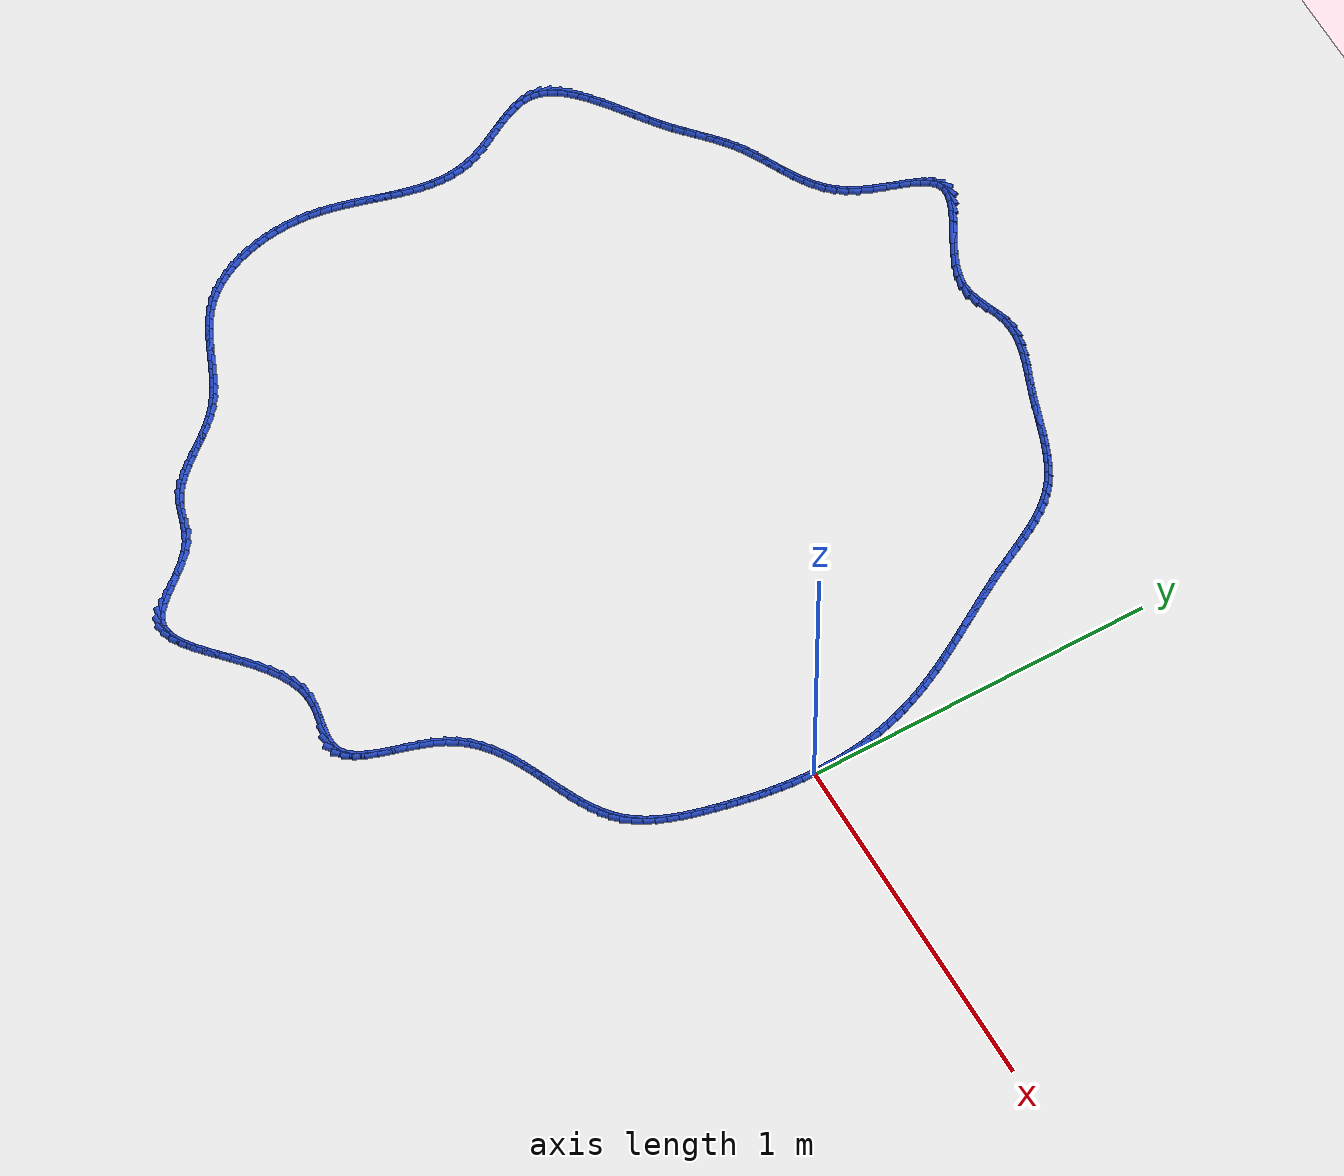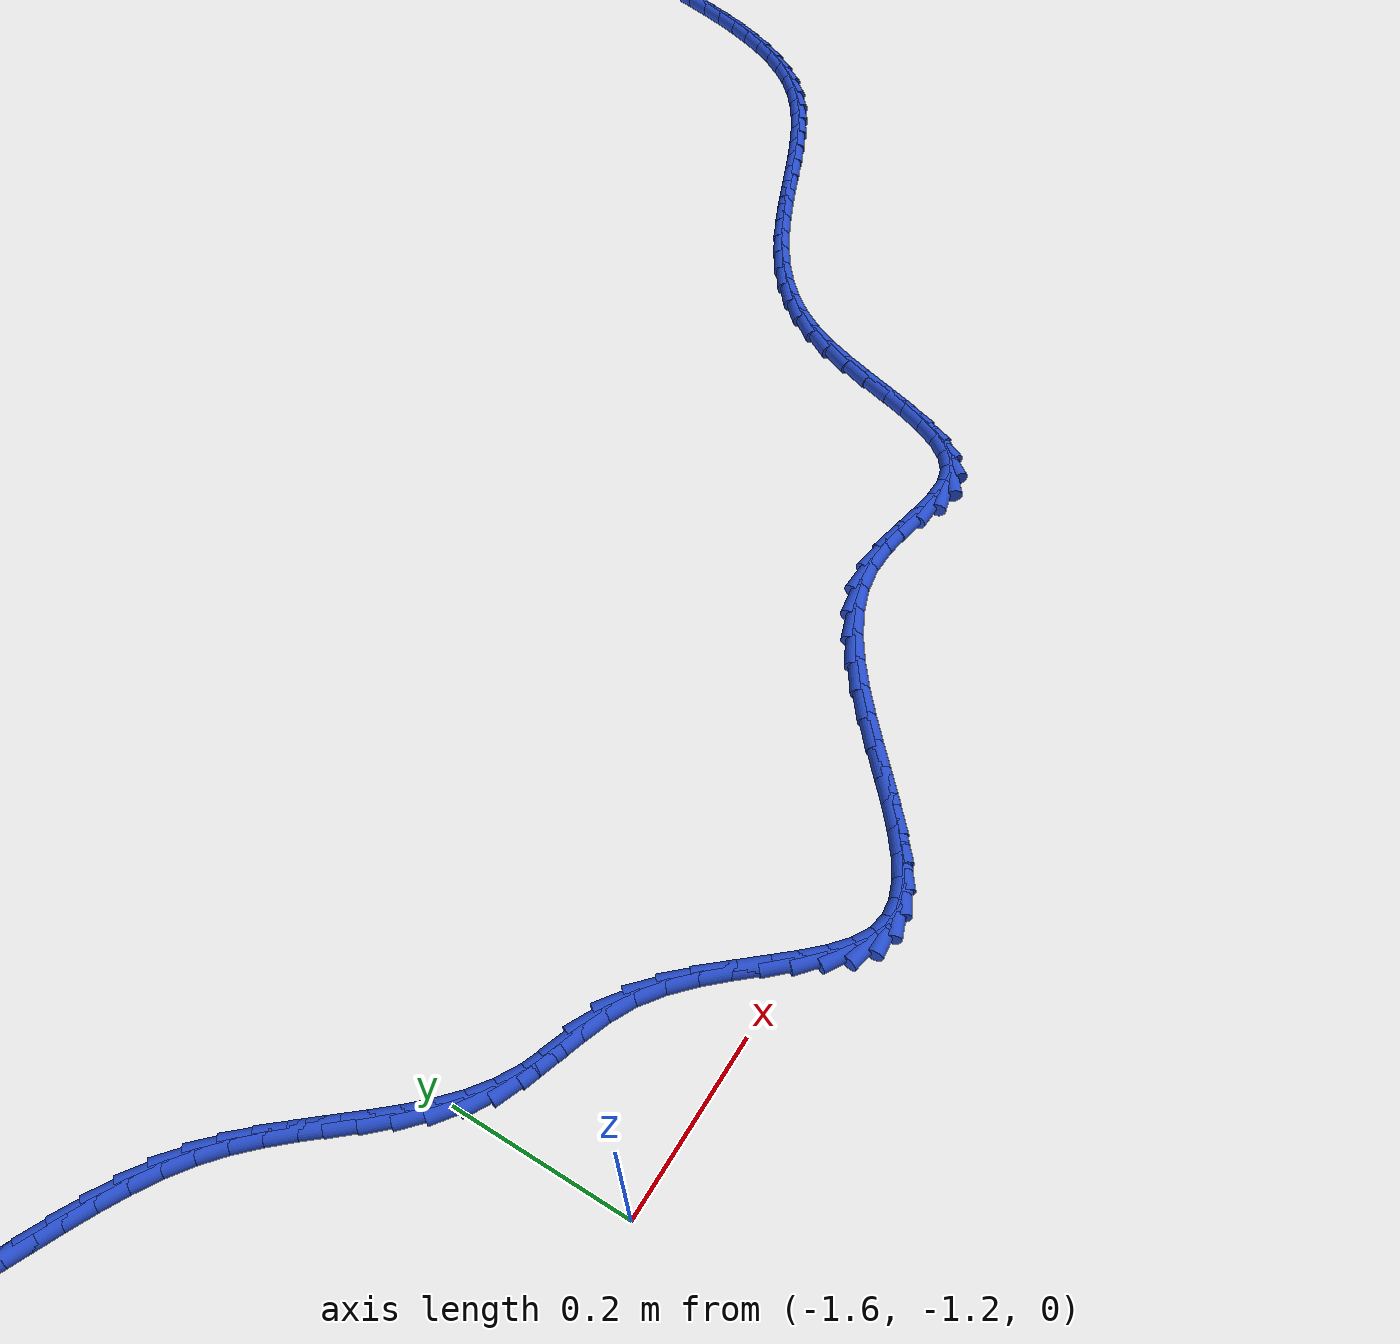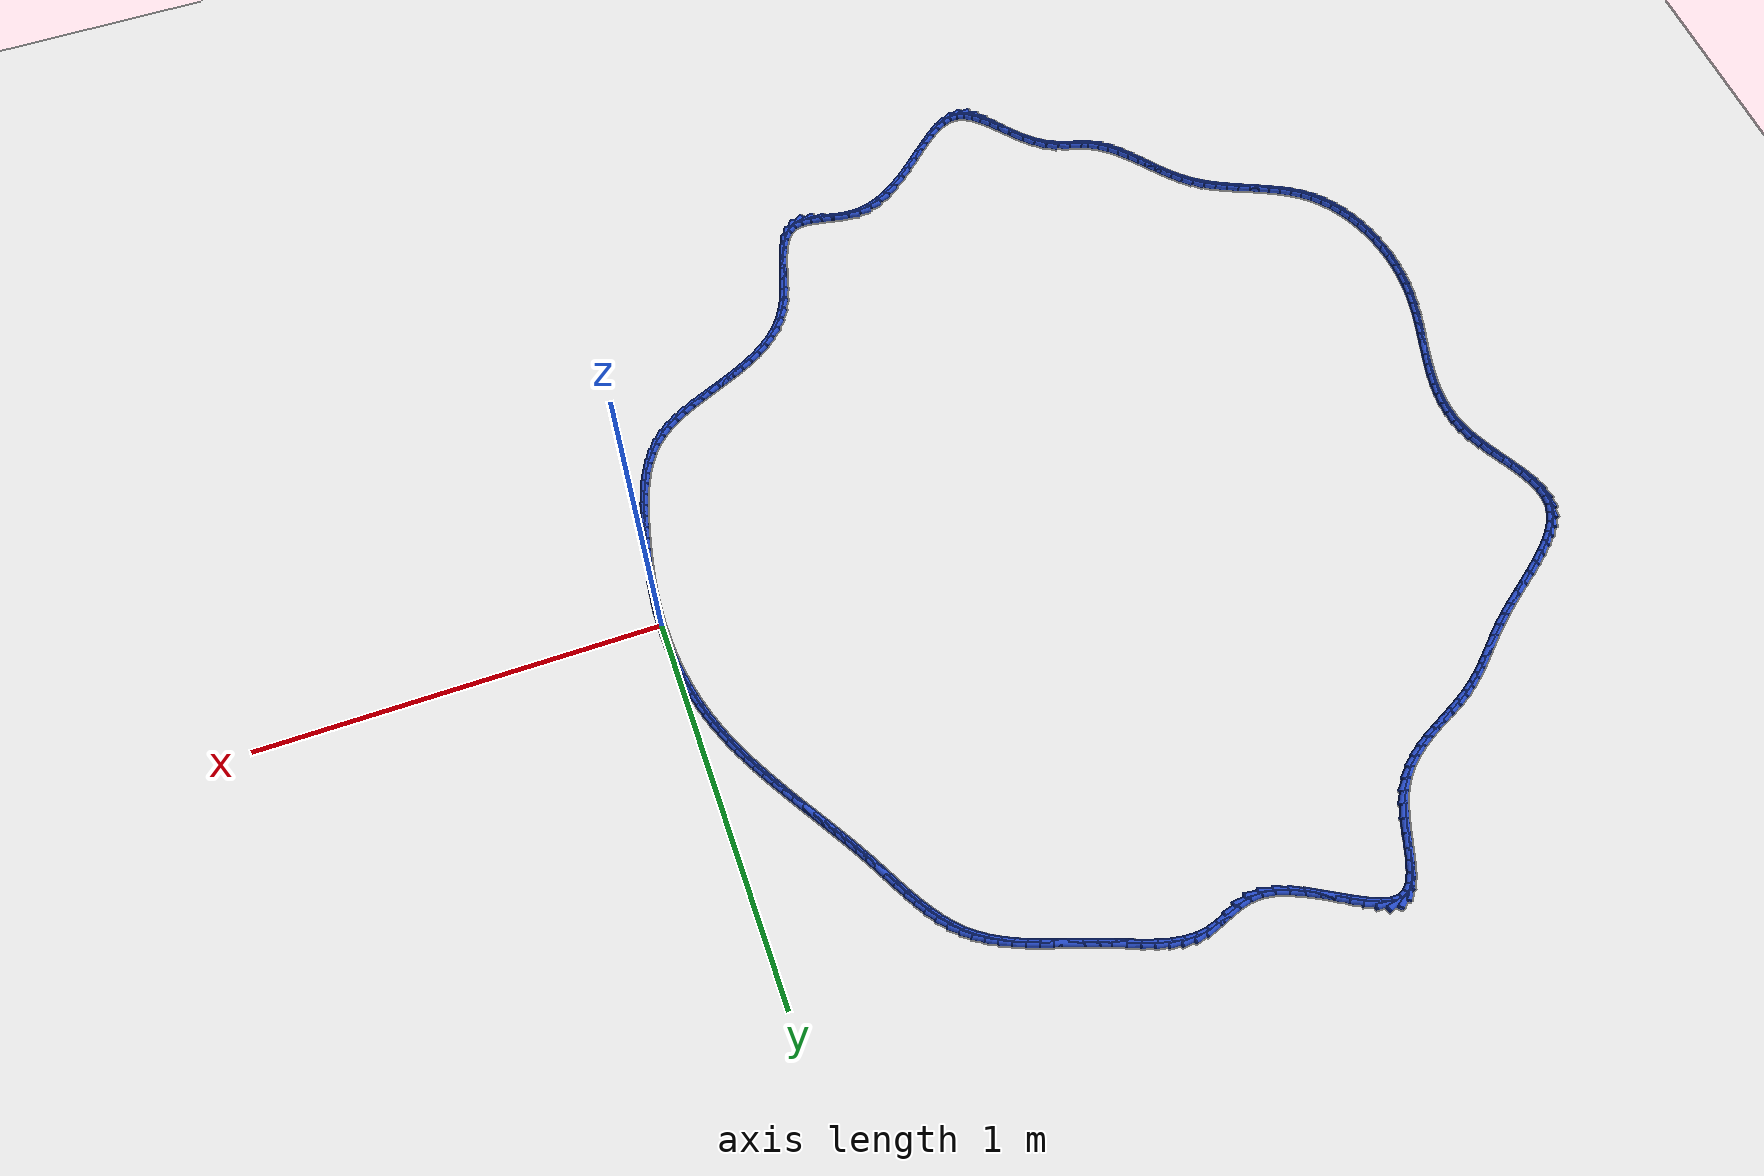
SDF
<sdf version="1.6">
 <world name="default">
  <light name="sun" type="directional">
   <pose>0 0 10 0 -0 0</pose>
   <diffuse>0.8 0.8 0.8 1</diffuse>
   <specular>0.2 0.2 0.2 1</specular>
   <attenuation>
    <range>1000</range>
    <constant>0.9</constant>
    <linear>0.01</linear>
    <quadratic>0.001</quadratic>
   </attenuation>
   <direction>-0.5 0.1 -0.9</direction>
  </light>
  <model name="ground_plane">
   <static>1</static>
   <link name="link">
    <collision name="collision">
     <geometry><plane><normal>0 0 1</normal><size>100 100</size></plane></geometry>
     <surface><friction><ode><mu>100</mu><mu2>50</mu2></ode></friction></surface>
    </collision>
    <visual name="visual">
     <cast_shadows>0</cast_shadows>
     <geometry><plane><normal>0 0 1</normal><size>100 100</size></plane></geometry>
     <material>
      <script><uri>file://media/materials/scripts/gazebo.material</uri><name>Gazebo/WhiteGlow</name></script>
     </material>
    </visual>
   </link>
  </model>
  <gravity>0 0 -9.8</gravity>
  <magnetic_field>6e-06 2.3e-05 -4.2e-05</magnetic_field>
  <atmosphere type="adiabatic"/>
  <physics name="default_physics" default="0" type="ode">
   <max_step_size>0.001</max_step_size>
   <real_time_factor>1</real_time_factor>
   <real_time_update_rate>1000</real_time_update_rate>
  </physics>
  <scene><ambient>0.4 0.4 0.4 1</ambient><background>0.7 0.7 0.7 1</background><shadows>1</shadows></scene>
  <spherical_coordinates>
   <surface_model>EARTH_WGS84</surface_model>
   <latitude_deg>0</latitude_deg>
   <longitude_deg>0</longitude_deg>
   <elevation>0</elevation>
   <heading_deg>0</heading_deg>
  </spherical_coordinates>
  <model name="line">
   <link name="link_0">
    <pose>4.336808689942018e-18 2.0816681711721685e-17 0.01 0 1.57 -1.569869605199208</pose>
    <collision name="collision">
     <geometry><cylinder><radius>0.01</radius><length>0.08</length></cylinder></geometry>
    </collision>
    <visual name="visual">
     <material>
      <script><name>Gazebo/Blue</name><uri>file://media/materials/scripts/gazebo.material</uri></script>
     </material>
     <geometry><cylinder><radius>0.01</radius><length>0.08</length></cylinder></geometry>
    </visual>
   </link>
   <link name="link_1">
    <pose>-2.8199256187058857e-05 0.03042903957955117 0.01 0 1.57 -1.536904389241077</pose>
    <collision name="collision">
     <geometry><cylinder><radius>0.01</radius><length>0.08</length></cylinder></geometry>
    </collision>
    <visual name="visual">
     <material>
      <script><name>Gazebo/Blue</name><uri>file://media/materials/scripts/gazebo.material</uri></script>
     </material>
     <geometry><cylinder><radius>0.01</radius><length>0.08</length></cylinder></geometry>
    </visual>
   </link>
   <link name="link_2">
    <pose>-0.001064233398030973 0.06098608356603939 0.01 0 1.57 -1.5035891266264223</pose>
    <collision name="collision">
     <geometry><cylinder><radius>0.01</radius><length>0.08</length></cylinder></geometry>
    </collision>
    <visual name="visual">
     <material>
      <script><name>Gazebo/Blue</name><uri>file://media/materials/scripts/gazebo.material</uri></script>
     </material>
     <geometry><cylinder><radius>0.01</radius><length>0.08</length></cylinder></geometry>
    </visual>
   </link>
   <link name="link_3">
    <pose>-0.003123707860153108 0.09158359057112793 0.01 0 1.57 -1.4697188301909914</pose>
    <collision name="collision">
     <geometry><cylinder><radius>0.01</radius><length>0.08</length></cylinder></geometry>
    </collision>
    <visual name="visual">
     <material>
      <script><name>Gazebo/Blue</name><uri>file://media/materials/scripts/gazebo.material</uri></script>
     </material>
     <geometry><cylinder><radius>0.01</radius><length>0.08</length></cylinder></geometry>
    </visual>
   </link>
   <link name="link_4">
    <pose>-0.006222228077174839 0.12213401920648005 0.01 0 1.57 -1.4350891189731654</pose>
    <collision name="collision">
     <geometry><cylinder><radius>0.01</radius><length>0.08</length></cylinder></geometry>
    </collision>
    <visual name="visual">
     <material>
      <script><name>Gazebo/Blue</name><uri>file://media/materials/scripts/gazebo.material</uri></script>
     </material>
     <geometry><cylinder><radius>0.01</radius><length>0.08</length></cylinder></geometry>
    </visual>
   </link>
   <link name="link_5">
    <pose>-0.010375399483717532 0.15254982808375903 0.01 0 1.57 -1.3994942355185533</pose>
    <collision name="collision">
     <geometry><cylinder><radius>0.01</radius><length>0.08</length></cylinder></geometry>
    </collision>
    <visual name="visual">
     <material>
      <script><name>Gazebo/Blue</name><uri>file://media/materials/scripts/gazebo.material</uri></script>
     </material>
     <geometry><cylinder><radius>0.01</radius><length>0.08</length></cylinder></geometry>
    </visual>
   </link>
   <link name="link_6">
    <pose>-0.015598827514402558 0.18274347581462813 0.01 0 1.57 -1.3627255431534695</pose>
    <collision name="collision">
     <geometry><cylinder><radius>0.01</radius><length>0.08</length></cylinder></geometry>
    </collision>
    <visual name="visual">
     <material>
      <script><name>Gazebo/Blue</name><uri>file://media/materials/scripts/gazebo.material</uri></script>
     </material>
     <geometry><cylinder><radius>0.01</radius><length>0.08</length></cylinder></geometry>
    </visual>
   </link>
   <link name="link_7">
    <pose>-0.021908117603851286 0.2126274210107506 0.01 0 1.57 -1.324570599079978</pose>
    <collision name="collision">
     <geometry><cylinder><radius>0.01</radius><length>0.08</length></cylinder></geometry>
    </collision>
    <visual name="visual">
     <material>
      <script><name>Gazebo/Blue</name><uri>file://media/materials/scripts/gazebo.material</uri></script>
     </material>
     <geometry><cylinder><radius>0.01</radius><length>0.08</length></cylinder></geometry>
    </visual>
   </link>
   <link name="link_8">
    <pose>-0.029318875186685085 0.2421141222837896 0.01 0 1.57 -1.2848718118222824</pose>
    <collision name="collision">
     <geometry><cylinder><radius>0.01</radius><length>0.08</length></cylinder></geometry>
    </collision>
    <visual name="visual">
     <material>
      <script><name>Gazebo/Blue</name><uri>file://media/materials/scripts/gazebo.material</uri></script>
     </material>
     <geometry><cylinder><radius>0.01</radius><length>0.08</length></cylinder></geometry>
    </visual>
   </link>
   <link name="link_9">
    <pose>-0.03784538438092388 0.27111785237308156 0.01 0 1.57 -1.2454574519196293</pose>
    <collision name="collision">
     <geometry><cylinder><radius>0.01</radius><length>0.08</length></cylinder></geometry>
    </collision>
    <visual name="visual">
     <material>
      <script><name>Gazebo/Blue</name><uri>file://media/materials/scripts/gazebo.material</uri></script>
     </material>
     <geometry><cylinder><radius>0.01</radius><length>0.08</length></cylinder></geometry>
    </visual>
   </link>
   <link name="link_10">
    <pose>-0.04745771358151395 0.29961359086651795 0.01 0 1.57 -1.208871732727496</pose>
    <collision name="collision">
     <geometry><cylinder><radius>0.01</radius><length>0.08</length></cylinder></geometry>
    </collision>
    <visual name="visual">
     <material>
      <script><name>Gazebo/Blue</name><uri>file://media/materials/scripts/gazebo.material</uri></script>
     </material>
     <geometry><cylinder><radius>0.01</radius><length>0.08</length></cylinder></geometry>
    </visual>
   </link>
   <link name="link_11">
    <pose>-0.0580723182726139 0.3276499262546498 0.01 0 1.57 -1.1754614668483574</pose>
    <collision name="collision">
     <geometry><cylinder><radius>0.01</radius><length>0.08</length></cylinder></geometry>
    </collision>
    <visual name="visual">
     <material>
      <script><name>Gazebo/Blue</name><uri>file://media/materials/scripts/gazebo.material</uri></script>
     </material>
     <geometry><cylinder><radius>0.01</radius><length>0.08</length></cylinder></geometry>
    </visual>
   </link>
   <link name="link_12">
    <pose>-0.0696024312775198 0.3552798716437836 0.01 0 1.57 -1.1453722685918644</pose>
    <collision name="collision">
     <geometry><cylinder><radius>0.01</radius><length>0.08</length></cylinder></geometry>
    </collision>
    <visual name="visual">
     <material>
      <script><name>Gazebo/Blue</name><uri>file://media/materials/scripts/gazebo.material</uri></script>
     </material>
     <geometry><cylinder><radius>0.01</radius><length>0.08</length></cylinder></geometry>
    </visual>
   </link>
   <link name="link_13">
    <pose>-0.08196128541952764 0.38255644014022533 0.01 0 1.57 -1.118699451016616</pose>
    <collision name="collision">
     <geometry><cylinder><radius>0.01</radius><length>0.08</length></cylinder></geometry>
    </collision>
    <visual name="visual">
     <material>
      <script><name>Gazebo/Blue</name><uri>file://media/materials/scripts/gazebo.material</uri></script>
     </material>
     <geometry><cylinder><radius>0.01</radius><length>0.08</length></cylinder></geometry>
    </visual>
   </link>
   <link name="link_14">
    <pose>-0.09506211352193349 0.4095326448502814 0.01 0 1.57 -1.0954966320516033</pose>
    <collision name="collision">
     <geometry><cylinder><radius>0.01</radius><length>0.08</length></cylinder></geometry>
    </collision>
    <visual name="visual">
     <material>
      <script><name>Gazebo/Blue</name><uri>file://media/materials/scripts/gazebo.material</uri></script>
     </material>
     <geometry><cylinder><radius>0.01</radius><length>0.08</length></cylinder></geometry>
    </visual>
   </link>
   <link name="link_15">
    <pose>-0.10881814840803339 0.43626149888025795 0.01 0 1.57 -1.075784581439223</pose>
    <collision name="collision">
     <geometry><cylinder><radius>0.01</radius><length>0.08</length></cylinder></geometry>
    </collision>
    <visual name="visual">
     <material>
      <script><name>Gazebo/Blue</name><uri>file://media/materials/scripts/gazebo.material</uri></script>
     </material>
     <geometry><cylinder><radius>0.01</radius><length>0.08</length></cylinder></geometry>
    </visual>
   </link>
   <link name="link_16">
    <pose>-0.12314262290112332 0.46279601533646125 0.01 0 1.57 -1.0595595638065634</pose>
    <collision name="collision">
     <geometry><cylinder><radius>0.01</radius><length>0.08</length></cylinder></geometry>
    </collision>
    <visual name="visual">
     <material>
      <script><name>Gazebo/Blue</name><uri>file://media/materials/scripts/gazebo.material</uri></script>
     </material>
     <geometry><cylinder><radius>0.01</radius><length>0.08</length></cylinder></geometry>
    </visual>
   </link>
   <link name="link_17">
    <pose>-0.13794876982449938 0.48918920732519766 0.01 0 1.57 -1.0468006930487492</pose>
    <collision name="collision">
     <geometry><cylinder><radius>0.01</radius><length>0.08</length></cylinder></geometry>
    </collision>
    <visual name="visual">
     <material>
      <script><name>Gazebo/Blue</name><uri>file://media/materials/scripts/gazebo.material</uri></script>
     </material>
     <geometry><cylinder><radius>0.01</radius><length>0.08</length></cylinder></geometry>
    </visual>
   </link>
   <link name="link_18">
    <pose>-0.1531498220014576 0.5154940879527733 0.01 0 1.57 -1.0374760321924663</pose>
    <collision name="collision">
     <geometry><cylinder><radius>0.01</radius><length>0.08</length></cylinder></geometry>
    </collision>
    <visual name="visual">
     <material>
      <script><name>Gazebo/Blue</name><uri>file://media/materials/scripts/gazebo.material</uri></script>
     </material>
     <geometry><cylinder><radius>0.01</radius><length>0.08</length></cylinder></geometry>
    </visual>
   </link>
   <link name="link_19">
    <pose>-0.16865901225529395 0.5417636703254942 0.01 0 1.57 -1.0315473351146687</pose>
    <collision name="collision">
     <geometry><cylinder><radius>0.01</radius><length>0.08</length></cylinder></geometry>
    </collision>
    <visual name="visual">
     <material>
      <script><name>Gazebo/Blue</name><uri>file://media/materials/scripts/gazebo.material</uri></script>
     </material>
     <geometry><cylinder><radius>0.01</radius><length>0.08</length></cylinder></geometry>
    </visual>
   </link>
   <link name="link_20">
    <pose>-0.18438957340930456 0.568050967549667 0.01 0 1.57 -1.0289734326760365</pose>
    <collision name="collision">
     <geometry><cylinder><radius>0.01</radius><length>0.08</length></cylinder></geometry>
    </collision>
    <visual name="visual">
     <material>
      <script><name>Gazebo/Blue</name><uri>file://media/materials/scripts/gazebo.material</uri></script>
     </material>
     <geometry><cylinder><radius>0.01</radius><length>0.08</length></cylinder></geometry>
    </visual>
   </link>
   <link name="link_21">
    <pose>-0.20025473828678547 0.5944089927315978 0.01 0 1.57 -1.0297123258085692</pose>
    <collision name="collision">
     <geometry><cylinder><radius>0.01</radius><length>0.08</length></cylinder></geometry>
    </collision>
    <visual name="visual">
     <material>
      <script><name>Gazebo/Blue</name><uri>file://media/materials/scripts/gazebo.material</uri></script>
     </material>
     <geometry><cylinder><radius>0.01</radius><length>0.08</length></cylinder></geometry>
    </visual>
   </link>
   <link name="link_22">
    <pose>-0.2161677397110326 0.6208907589775927 0.01 0 1.57 -1.0337220750700191</pose>
    <collision name="collision">
     <geometry><cylinder><radius>0.01</radius><length>0.08</length></cylinder></geometry>
    </collision>
    <visual name="visual">
     <material>
      <script><name>Gazebo/Blue</name><uri>file://media/materials/scripts/gazebo.material</uri></script>
     </material>
     <geometry><cylinder><radius>0.01</radius><length>0.08</length></cylinder></geometry>
    </visual>
   </link>
   <link name="link_23">
    <pose>-0.23204181050534212 0.6475492793939581 0.01 0 1.57 -1.04096058332692</pose>
    <collision name="collision">
     <geometry><cylinder><radius>0.01</radius><length>0.08</length></cylinder></geometry>
    </collision>
    <visual name="visual">
     <material>
      <script><name>Gazebo/Blue</name><uri>file://media/materials/scripts/gazebo.material</uri></script>
     </material>
     <geometry><cylinder><radius>0.01</radius><length>0.08</length></cylinder></geometry>
    </visual>
   </link>
   <link name="link_24">
    <pose>-0.24779018349301002 0.6744375670870003 0.01 0 1.57 -1.0513843671418859</pose>
    <collision name="collision">
     <geometry><cylinder><radius>0.01</radius><length>0.08</length></cylinder></geometry>
    </collision>
    <visual name="visual">
     <material>
      <script><name>Gazebo/Blue</name><uri>file://media/materials/scripts/gazebo.material</uri></script>
     </material>
     <geometry><cylinder><radius>0.01</radius><length>0.08</length></cylinder></geometry>
    </visual>
   </link>
   <link name="link_25">
    <pose>-0.26332609149733227 0.7016086351630252 0.01 0 1.57 -1.064946412656028</pose>
    <collision name="collision">
     <geometry><cylinder><radius>0.01</radius><length>0.08</length></cylinder></geometry>
    </collision>
    <visual name="visual">
     <material>
      <script><name>Gazebo/Blue</name><uri>file://media/materials/scripts/gazebo.material</uri></script>
     </material>
     <geometry><cylinder><radius>0.01</radius><length>0.08</length></cylinder></geometry>
    </visual>
   </link>
   <link name="link_26">
    <pose>-0.27856276734160496 0.7291154967283394 0.01 0 1.57 -1.081235776814421</pose>
    <collision name="collision">
     <geometry><cylinder><radius>0.01</radius><length>0.08</length></cylinder></geometry>
    </collision>
    <visual name="visual">
     <material>
      <script><name>Gazebo/Blue</name><uri>file://media/materials/scripts/gazebo.material</uri></script>
     </material>
     <geometry><cylinder><radius>0.01</radius><length>0.08</length></cylinder></geometry>
    </visual>
   </link>
   <link name="link_27">
    <pose>-0.2934216428789661 0.7570025307242144 0.01 0 1.57 -1.0925038113711276</pose>
    <collision name="collision">
     <geometry><cylinder><radius>0.01</radius><length>0.08</length></cylinder></geometry>
    </collision>
    <visual name="visual">
     <material>
      <script><name>Gazebo/Blue</name><uri>file://media/materials/scripts/gazebo.material</uri></script>
     </material>
     <geometry><cylinder><radius>0.01</radius><length>0.08</length></cylinder></geometry>
    </visual>
   </link>
   <link name="link_28">
    <pose>-0.30800230620377717 0.785126504823479 0.01 0 1.57 -1.091392560817019</pose>
    <collision name="collision">
     <geometry><cylinder><radius>0.01</radius><length>0.08</length></cylinder></geometry>
    </collision>
    <visual name="visual">
     <material>
      <script><name>Gazebo/Blue</name><uri>file://media/materials/scripts/gazebo.material</uri></script>
     </material>
     <geometry><cylinder><radius>0.01</radius><length>0.08</length></cylinder></geometry>
    </visual>
   </link>
   <link name="link_29">
    <pose>-0.3225768973745958 0.8131624771351955 0.01 0 1.57 -1.0774780381619946</pose>
    <collision name="collision">
     <geometry><cylinder><radius>0.01</radius><length>0.08</length></cylinder></geometry>
    </collision>
    <visual name="visual">
     <material>
      <script><name>Gazebo/Blue</name><uri>file://media/materials/scripts/gazebo.material</uri></script>
     </material>
     <geometry><cylinder><radius>0.01</radius><length>0.08</length></cylinder></geometry>
    </visual>
   </link>
   <link name="link_30">
    <pose>-0.3374246342654462 0.8407780523223456 0.01 0 1.57 -1.050249906386674</pose>
    <collision name="collision">
     <geometry><cylinder><radius>0.01</radius><length>0.08</length></cylinder></geometry>
    </collision>
    <visual name="visual">
     <material>
      <script><name>Gazebo/Blue</name><uri>file://media/materials/scripts/gazebo.material</uri></script>
     </material>
     <geometry><cylinder><radius>0.01</radius><length>0.08</length></cylinder></geometry>
    </visual>
   </link>
   <link name="link_31">
    <pose>-0.35282473475035364 0.8676408350479127 0.01 0 1.57 -1.0088374173672885</pose>
    <collision name="collision">
     <geometry><cylinder><radius>0.01</radius><length>0.08</length></cylinder></geometry>
    </collision>
    <visual name="visual">
     <material>
      <script><name>Gazebo/Blue</name><uri>file://media/materials/scripts/gazebo.material</uri></script>
     </material>
     <geometry><cylinder><radius>0.01</radius><length>0.08</length></cylinder></geometry>
    </visual>
   </link>
   <link name="link_32">
    <pose>-0.3690564167033428 0.8934184299748793 0.01 0 1.57 -0.9521123101027495</pose>
    <collision name="collision">
     <geometry><cylinder><radius>0.01</radius><length>0.08</length></cylinder></geometry>
    </collision>
    <visual name="visual">
     <material>
      <script><name>Gazebo/Blue</name><uri>file://media/materials/scripts/gazebo.material</uri></script>
     </material>
     <geometry><cylinder><radius>0.01</radius><length>0.08</length></cylinder></geometry>
    </visual>
   </link>
   <link name="link_33">
    <pose>-0.3863988979984385 0.9177784417662279 0.01 0 1.57 -0.8789150454142938</pose>
    <collision name="collision">
     <geometry><cylinder><radius>0.01</radius><length>0.08</length></cylinder></geometry>
    </collision>
    <visual name="visual">
     <material>
      <script><name>Gazebo/Blue</name><uri>file://media/materials/scripts/gazebo.material</uri></script>
     </material>
     <geometry><cylinder><radius>0.01</radius><length>0.08</length></cylinder></geometry>
    </visual>
   </link>
   <link name="link_34">
    <pose>-0.40513139650966523 0.9403884750849406 0.01 0 1.57 -0.7884748871449913</pose>
    <collision name="collision">
     <geometry><cylinder><radius>0.01</radius><length>0.08</length></cylinder></geometry>
    </collision>
    <visual name="visual">
     <material>
      <script><name>Gazebo/Blue</name><uri>file://media/materials/scripts/gazebo.material</uri></script>
     </material>
     <geometry><cylinder><radius>0.01</radius><length>0.08</length></cylinder></geometry>
    </visual>
   </link>
   <link name="link_35">
    <pose>-0.4255331288579504 0.9609161362676324 0.01 0 1.57 -0.686061484330302</pose>
    <collision name="collision">
     <geometry><cylinder><radius>0.01</radius><length>0.08</length></cylinder></geometry>
    </collision>
    <visual name="visual">
     <material>
      <script><name>Gazebo/Blue</name><uri>file://media/materials/scripts/gazebo.material</uri></script>
     </material>
     <geometry><cylinder><radius>0.01</radius><length>0.08</length></cylinder></geometry>
    </visual>
   </link>
   <link name="link_36">
    <pose>-0.4477969704075304 0.9791443486795252 0.01 0 1.57 -0.5920509151765315</pose>
    <collision name="collision">
     <geometry><cylinder><radius>0.01</radius><length>0.08</length></cylinder></geometry>
    </collision>
    <visual name="visual">
     <material>
      <script><name>Gazebo/Blue</name><uri>file://media/materials/scripts/gazebo.material</uri></script>
     </material>
     <geometry><cylinder><radius>0.01</radius><length>0.08</length></cylinder></geometry>
    </visual>
   </link>
   <link name="link_37">
    <pose>-0.47179537082136486 0.9952839949393533 0.01 0 1.57 -0.5123888260326118</pose>
    <collision name="collision">
     <geometry><cylinder><radius>0.01</radius><length>0.08</length></cylinder></geometry>
    </collision>
    <visual name="visual">
     <material>
      <script><name>Gazebo/Blue</name><uri>file://media/materials/scripts/gazebo.material</uri></script>
     </material>
     <geometry><cylinder><radius>0.01</radius><length>0.08</length></cylinder></geometry>
    </visual>
   </link>
   <link name="link_38">
    <pose>-0.49732646397833413 1.0096452135225182 0.01 0 1.57 -0.4474960084580683</pose>
    <collision name="collision">
     <geometry><cylinder><radius>0.01</radius><length>0.08</length></cylinder></geometry>
    </collision>
    <visual name="visual">
     <material>
      <script><name>Gazebo/Blue</name><uri>file://media/materials/scripts/gazebo.material</uri></script>
     </material>
     <geometry><cylinder><radius>0.01</radius><length>0.08</length></cylinder></geometry>
    </visual>
   </link>
   <link name="link_39">
    <pose>-0.5241883837573194 1.022538142904422 0.01 0 1.57 -0.39697819226219205</pose>
    <collision name="collision">
     <geometry><cylinder><radius>0.01</radius><length>0.08</length></cylinder></geometry>
    </collision>
    <visual name="visual">
     <material>
      <script><name>Gazebo/Blue</name><uri>file://media/materials/scripts/gazebo.material</uri></script>
     </material>
     <geometry><cylinder><radius>0.01</radius><length>0.08</length></cylinder></geometry>
    </visual>
   </link>
   <link name="link_40">
    <pose>-0.5521792640372009 1.0342729215604665 0.01 0 1.57 -0.360059313446639</pose>
    <collision name="collision">
     <geometry><cylinder><radius>0.01</radius><length>0.08</length></cylinder></geometry>
    </collision>
    <visual name="visual">
     <material>
      <script><name>Gazebo/Blue</name><uri>file://media/materials/scripts/gazebo.material</uri></script>
     </material>
     <geometry><cylinder><radius>0.01</radius><length>0.08</length></cylinder></geometry>
    </visual>
   </link>
   <link name="link_41">
    <pose>-0.5810972386968598 1.0451596879660532 0.01 0 1.57 -0.3358863589384313</pose>
    <collision name="collision">
     <geometry><cylinder><radius>0.01</radius><length>0.08</length></cylinder></geometry>
    </collision>
    <visual name="visual">
     <material>
      <script><name>Gazebo/Blue</name><uri>file://media/materials/scripts/gazebo.material</uri></script>
     </material>
     <geometry><cylinder><radius>0.01</radius><length>0.08</length></cylinder></geometry>
    </visual>
   </link>
   <link name="link_42">
    <pose>-0.6107404416151766 1.055508580596584 0.01 0 1.57 -0.3237074716809988</pose>
    <collision name="collision">
     <geometry><cylinder><radius>0.01</radius><length>0.08</length></cylinder></geometry>
    </collision>
    <visual name="visual">
     <material>
      <script><name>Gazebo/Blue</name><uri>file://media/materials/scripts/gazebo.material</uri></script>
     </material>
     <geometry><cylinder><radius>0.01</radius><length>0.08</length></cylinder></geometry>
    </visual>
   </link>
   <link name="link_43">
    <pose>-0.6409070066710321 1.0656297379274606 0.01 0 1.57 -0.32295664379776373</pose>
    <collision name="collision">
     <geometry><cylinder><radius>0.01</radius><length>0.08</length></cylinder></geometry>
    </collision>
    <visual name="visual">
     <material>
      <script><name>Gazebo/Blue</name><uri>file://media/materials/scripts/gazebo.material</uri></script>
     </material>
     <geometry><cylinder><radius>0.01</radius><length>0.08</length></cylinder></geometry>
    </visual>
   </link>
   <link name="link_44">
    <pose>-0.6713950677433072 1.0758332984340848 0.01 0 1.57 -0.3332773336003079</pose>
    <collision name="collision">
     <geometry><cylinder><radius>0.01</radius><length>0.08</length></cylinder></geometry>
    </collision>
    <visual name="visual">
     <material>
      <script><name>Gazebo/Blue</name><uri>file://media/materials/scripts/gazebo.material</uri></script>
     </material>
     <geometry><cylinder><radius>0.01</radius><length>0.08</length></cylinder></geometry>
    </visual>
   </link>
   <link name="link_45">
    <pose>-0.7020027587108822 1.0864294005918582 0.01 0 1.57 -0.3536466021407067</pose>
    <collision name="collision">
     <geometry><cylinder><radius>0.01</radius><length>0.08</length></cylinder></geometry>
    </collision>
    <visual name="visual">
     <material>
      <script><name>Gazebo/Blue</name><uri>file://media/materials/scripts/gazebo.material</uri></script>
     </material>
     <geometry><cylinder><radius>0.01</radius><length>0.08</length></cylinder></geometry>
    </visual>
   </link>
   <link name="link_46">
    <pose>-0.7325328604942872 1.0977000919589615 0.01 0 1.57 -0.36688571351195015</pose>
    <collision name="collision">
     <geometry><cylinder><radius>0.01</radius><length>0.08</length></cylinder></geometry>
    </collision>
    <visual name="visual">
     <material>
      <script><name>Gazebo/Blue</name><uri>file://media/materials/scripts/gazebo.material</uri></script>
     </material>
     <geometry><cylinder><radius>0.01</radius><length>0.08</length></cylinder></geometry>
    </visual>
   </link>
   <link name="link_47">
    <pose>-0.7628815845318117 1.1093626416519942 0.01 0 1.57 -0.3570950004985565</pose>
    <collision name="collision">
     <geometry><cylinder><radius>0.01</radius><length>0.08</length></cylinder></geometry>
    </collision>
    <visual name="visual">
     <material>
      <script><name>Gazebo/Blue</name><uri>file://media/materials/scripts/gazebo.material</uri></script>
     </material>
     <geometry><cylinder><radius>0.01</radius><length>0.08</length></cylinder></geometry>
    </visual>
   </link>
   <link name="link_48">
    <pose>-0.7930316596117738 1.1206113297761435 0.01 0 1.57 -0.3226596815610496</pose>
    <collision name="collision">
     <geometry><cylinder><radius>0.01</radius><length>0.08</length></cylinder></geometry>
    </collision>
    <visual name="visual">
     <material>
      <script><name>Gazebo/Blue</name><uri>file://media/materials/scripts/gazebo.material</uri></script>
     </material>
     <geometry><cylinder><radius>0.01</radius><length>0.08</length></cylinder></geometry>
    </visual>
   </link>
   <link name="link_49">
    <pose>-0.8229690763687596 1.13062071889146 0.01 0 1.57 -0.261286862628537</pose>
    <collision name="collision">
     <geometry><cylinder><radius>0.01</radius><length>0.08</length></cylinder></geometry>
    </collision>
    <visual name="visual">
     <material>
      <script><name>Gazebo/Blue</name><uri>file://media/materials/scripts/gazebo.material</uri></script>
     </material>
     <geometry><cylinder><radius>0.01</radius><length>0.08</length></cylinder></geometry>
    </visual>
   </link>
   <link name="link_50">
    <pose>-0.8526798254373542 1.1385653715579933 0.01 0 1.57 -0.1698595762940577</pose>
    <collision name="collision">
     <geometry><cylinder><radius>0.01</radius><length>0.08</length></cylinder></geometry>
    </collision>
    <visual name="visual">
     <material>
      <script><name>Gazebo/Blue</name><uri>file://media/materials/scripts/gazebo.material</uri></script>
     </material>
     <geometry><cylinder><radius>0.01</radius><length>0.08</length></cylinder></geometry>
    </visual>
   </link>
   <link name="link_51">
    <pose>-0.8821498974521432 1.143619850335793 0.01 0 1.57 -0.045795437010591265</pose>
    <collision name="collision">
     <geometry><cylinder><radius>0.01</radius><length>0.08</length></cylinder></geometry>
    </collision>
    <visual name="visual">
     <material>
      <script><name>Gazebo/Blue</name><uri>file://media/materials/scripts/gazebo.material</uri></script>
     </material>
     <geometry><cylinder><radius>0.01</radius><length>0.08</length></cylinder></geometry>
    </visual>
   </link>
   <link name="link_52">
    <pose>-0.9113652830477125 1.1449587177849092 0.01 0 1.57 0.11017543452837951</pose>
    <collision name="collision">
     <geometry><cylinder><radius>0.01</radius><length>0.08</length></cylinder></geometry>
    </collision>
    <visual name="visual">
     <material>
      <script><name>Gazebo/Blue</name><uri>file://media/materials/scripts/gazebo.material</uri></script>
     </material>
     <geometry><cylinder><radius>0.01</radius><length>0.08</length></cylinder></geometry>
    </visual>
   </link>
   <link name="link_53">
    <pose>-0.9403119728586468 1.1417565364653912 0.01 0 1.57 0.2736359876907536</pose>
    <collision name="collision">
     <geometry><cylinder><radius>0.01</radius><length>0.08</length></cylinder></geometry>
    </collision>
    <visual name="visual">
     <material>
      <script><name>Gazebo/Blue</name><uri>file://media/materials/scripts/gazebo.material</uri></script>
     </material>
     <geometry><cylinder><radius>0.01</radius><length>0.08</length></cylinder></geometry>
    </visual>
   </link>
   <link name="link_54">
    <pose>-0.969020926816285 1.1336986053773777 0.01 0 1.57 0.3597674571014708</pose>
    <collision name="collision">
     <geometry><cylinder><radius>0.01</radius><length>0.08</length></cylinder></geometry>
    </collision>
    <visual name="visual">
     <material>
      <script><name>Gazebo/Blue</name><uri>file://media/materials/scripts/gazebo.material</uri></script>
     </material>
     <geometry><cylinder><radius>0.01</radius><length>0.08</length></cylinder></geometry>
    </visual>
   </link>
   <link name="link_55">
    <pose>-0.9977368201905479 1.1228974843211486 0.01 0 1.57 0.3534706112127885</pose>
    <collision name="collision">
     <geometry><cylinder><radius>0.01</radius><length>0.08</length></cylinder></geometry>
    </collision>
    <visual name="visual">
     <material>
      <script><name>Gazebo/Blue</name><uri>file://media/materials/scripts/gazebo.material</uri></script>
     </material>
     <geometry><cylinder><radius>0.01</radius><length>0.08</length></cylinder></geometry>
    </visual>
   </link>
   <link name="link_56">
    <pose>-1.026767749987862 1.112186042158194 0.01 0 1.57 0.2568529787826786</pose>
    <collision name="collision">
     <geometry><cylinder><radius>0.01</radius><length>0.08</length></cylinder></geometry>
    </collision>
    <visual name="visual">
     <material>
      <script><name>Gazebo/Blue</name><uri>file://media/materials/scripts/gazebo.material</uri></script>
     </material>
     <geometry><cylinder><radius>0.01</radius><length>0.08</length></cylinder></geometry>
    </visual>
   </link>
   <link name="link_57">
    <pose>-1.0564218233400802 1.1043972627489973 0.01 0 1.57 0.06773204795901323</pose>
    <collision name="collision">
     <geometry><cylinder><radius>0.01</radius><length>0.08</length></cylinder></geometry>
    </collision>
    <visual name="visual">
     <material>
      <script><name>Gazebo/Blue</name><uri>file://media/materials/scripts/gazebo.material</uri></script>
     </material>
     <geometry><cylinder><radius>0.01</radius><length>0.08</length></cylinder></geometry>
    </visual>
   </link>
   <link name="link_58">
    <pose>-1.0870003627364677 1.1023229426101866 0.01 0 1.57 -0.1475471825724006</pose>
    <collision name="collision">
     <geometry><cylinder><radius>0.01</radius><length>0.08</length></cylinder></geometry>
    </collision>
    <visual name="visual">
     <material>
      <script><name>Gazebo/Blue</name><uri>file://media/materials/scripts/gazebo.material</uri></script>
     </material>
     <geometry><cylinder><radius>0.01</radius><length>0.08</length></cylinder></geometry>
    </visual>
   </link>
   <link name="link_59">
    <pose>-1.1185167927824342 1.1070071444633494 0.01 0 1.57 -0.3058086887024668</pose>
    <collision name="collision">
     <geometry><cylinder><radius>0.01</radius><length>0.08</length></cylinder></geometry>
    </collision>
    <visual name="visual">
     <material>
      <script><name>Gazebo/Blue</name><uri>file://media/materials/scripts/gazebo.material</uri></script>
     </material>
     <geometry><cylinder><radius>0.01</radius><length>0.08</length></cylinder></geometry>
    </visual>
   </link>
   <link name="link_60">
    <pose>-1.150595948049343 1.1171349281578584 0.01 0 1.57 -0.41201638089441356</pose>
    <collision name="collision">
     <geometry><cylinder><radius>0.01</radius><length>0.08</length></cylinder></geometry>
    </collision>
    <visual name="visual">
     <material>
      <script><name>Gazebo/Blue</name><uri>file://media/materials/scripts/gazebo.material</uri></script>
     </material>
     <geometry><cylinder><radius>0.01</radius><length>0.08</length></cylinder></geometry>
    </visual>
   </link>
   <link name="link_61">
    <pose>-1.182835170463545 1.1312244546963202 0.01 0 1.57 -0.4778248007867314</pose>
    <collision name="collision">
     <geometry><cylinder><radius>0.01</radius><length>0.08</length></cylinder></geometry>
    </collision>
    <visual name="visual">
     <material>
      <script><name>Gazebo/Blue</name><uri>file://media/materials/scripts/gazebo.material</uri></script>
     </material>
     <geometry><cylinder><radius>0.01</radius><length>0.08</length></cylinder></geometry>
    </visual>
   </link>
   <link name="link_62">
    <pose>-1.214831801951392 1.1477938850813432 0.01 0 1.57 -0.51074860971089</pose>
    <collision name="collision">
     <geometry><cylinder><radius>0.01</radius><length>0.08</length></cylinder></geometry>
    </collision>
    <visual name="visual">
     <material>
      <script><name>Gazebo/Blue</name><uri>file://media/materials/scripts/gazebo.material</uri></script>
     </material>
     <geometry><cylinder><radius>0.01</radius><length>0.08</length></cylinder></geometry>
    </visual>
   </link>
   <link name="link_63">
    <pose>-1.2461831844392361 1.1653613803155345 0.01 0 1.57 -0.513341934159339</pose>
    <collision name="collision">
     <geometry><cylinder><radius>0.01</radius><length>0.08</length></cylinder></geometry>
    </collision>
    <visual name="visual">
     <material>
      <script><name>Gazebo/Blue</name><uri>file://media/materials/scripts/gazebo.material</uri></script>
     </material>
     <geometry><cylinder><radius>0.01</radius><length>0.08</length></cylinder></geometry>
    </visual>
   </link>
   <link name="link_64">
    <pose>-1.2764866598534277 1.182445101401501 0.01 0 1.57 -0.4826405321373303</pose>
    <collision name="collision">
     <geometry><cylinder><radius>0.01</radius><length>0.08</length></cylinder></geometry>
    </collision>
    <visual name="visual">
     <material>
      <script><name>Gazebo/Blue</name><uri>file://media/materials/scripts/gazebo.material</uri></script>
     </material>
     <geometry><cylinder><radius>0.01</radius><length>0.08</length></cylinder></geometry>
    </visual>
   </link>
   <link name="link_65">
    <pose>-1.3053395701203196 1.197563209341851 0.01 0 1.57 -0.4079966829494138</pose>
    <collision name="collision">
     <geometry><cylinder><radius>0.01</radius><length>0.08</length></cylinder></geometry>
    </collision>
    <visual name="visual">
     <material>
      <script><name>Gazebo/Blue</name><uri>file://media/materials/scripts/gazebo.material</uri></script>
     </material>
     <geometry><cylinder><radius>0.01</radius><length>0.08</length></cylinder></geometry>
    </visual>
   </link>
   <link name="link_66">
    <pose>-1.332339257166263 1.2092338651391914 0.01 0 1.57 -0.2659907479562023</pose>
    <collision name="collision">
     <geometry><cylinder><radius>0.01</radius><length>0.08</length></cylinder></geometry>
    </collision>
    <visual name="visual">
     <material>
      <script><name>Gazebo/Blue</name><uri>file://media/materials/scripts/gazebo.material</uri></script>
     </material>
     <geometry><cylinder><radius>0.01</radius><length>0.08</length></cylinder></geometry>
    </visual>
   </link>
   <link name="link_67">
    <pose>-1.3570830629176087 1.2159752297961304 0.01 0 1.57 -0.01495159284294088</pose>
    <collision name="collision">
     <geometry><cylinder><radius>0.01</radius><length>0.08</length></cylinder></geometry>
    </collision>
    <visual name="visual">
     <material>
      <script><name>Gazebo/Blue</name><uri>file://media/materials/scripts/gazebo.material</uri></script>
     </material>
     <geometry><cylinder><radius>0.01</radius><length>0.08</length></cylinder></geometry>
    </visual>
   </link>
   <link name="link_68">
    <pose>-1.379168329300709 1.2163054643152749 0.01 0 1.57 0.3768326548398783</pose>
    <collision name="collision">
     <geometry><cylinder><radius>0.01</radius><length>0.08</length></cylinder></geometry>
    </collision>
    <visual name="visual">
     <material>
      <script><name>Gazebo/Blue</name><uri>file://media/materials/scripts/gazebo.material</uri></script>
     </material>
     <geometry><cylinder><radius>0.01</radius><length>0.08</length></cylinder></geometry>
    </visual>
   </link>
   <link name="link_69">
    <pose>-1.3982037589802772 1.2087722936006464 0.01 0 1.57 0.7711398958925129</pose>
    <collision name="collision">
     <geometry><cylinder><radius>0.01</radius><length>0.08</length></cylinder></geometry>
    </collision>
    <visual name="visual">
     <material>
      <script><name>Gazebo/Blue</name><uri>file://media/materials/scripts/gazebo.material</uri></script>
     </material>
     <geometry><cylinder><radius>0.01</radius><length>0.08</length></cylinder></geometry>
    </visual>
   </link>
   <link name="link_70">
    <pose>-1.4142717390833326 1.1931561054606499 0.01 0 1.57 1.0154257907812452</pose>
    <collision name="collision">
     <geometry><cylinder><radius>0.01</radius><length>0.08</length></cylinder></geometry>
    </collision>
    <visual name="visual">
     <material>
      <script><name>Gazebo/Blue</name><uri>file://media/materials/scripts/gazebo.material</uri></script>
     </material>
     <geometry><cylinder><radius>0.01</radius><length>0.08</length></cylinder></geometry>
    </visual>
   </link>
   <link name="link_71">
    <pose>-1.428089192201496 1.1708885310755426 0.01 0 1.57 1.1476102558697054</pose>
    <collision name="collision">
     <geometry><cylinder><radius>0.01</radius><length>0.08</length></cylinder></geometry>
    </collision>
    <visual name="visual">
     <material>
      <script><name>Gazebo/Blue</name><uri>file://media/materials/scripts/gazebo.material</uri></script>
     </material>
     <geometry><cylinder><radius>0.01</radius><length>0.08</length></cylinder></geometry>
    </visual>
   </link>
   <link name="link_72">
    <pose>-1.4404174362641253 1.1435167310345187 0.01 0 1.57 1.2119681571283645</pose>
    <collision name="collision">
     <geometry><cylinder><radius>0.01</radius><length>0.08</length></cylinder></geometry>
    </collision>
    <visual name="visual">
     <material>
      <script><name>Gazebo/Blue</name><uri>file://media/materials/scripts/gazebo.material</uri></script>
     </material>
     <geometry><cylinder><radius>0.01</radius><length>0.08</length></cylinder></geometry>
    </visual>
   </link>
   <link name="link_73">
    <pose>-1.4520177892005763 1.1125878659267725 0.01 0 1.57 1.2312788049737375</pose>
    <collision name="collision">
     <geometry><cylinder><radius>0.01</radius><length>0.08</length></cylinder></geometry>
    </collision>
    <visual name="visual">
     <material>
      <script><name>Gazebo/Blue</name><uri>file://media/materials/scripts/gazebo.material</uri></script>
     </material>
     <geometry><cylinder><radius>0.01</radius><length>0.08</length></cylinder></geometry>
    </visual>
   </link>
   <link name="link_74">
    <pose>-1.4636515689402056 1.079649096341498 0.01 0 1.57 1.2145752423151026</pose>
    <collision name="collision">
     <geometry><cylinder><radius>0.01</radius><length>0.08</length></cylinder></geometry>
    </collision>
    <visual name="visual">
     <material>
      <script><name>Gazebo/Blue</name><uri>file://media/materials/scripts/gazebo.material</uri></script>
     </material>
     <geometry><cylinder><radius>0.01</radius><length>0.08</length></cylinder></geometry>
    </visual>
   </link>
   <link name="link_75">
    <pose>-1.4760800934123701 1.0462475828678903 0.01 0 1.57 1.162396304330501</pose>
    <collision name="collision">
     <geometry><cylinder><radius>0.01</radius><length>0.08</length></cylinder></geometry>
    </collision>
    <visual name="visual">
     <material>
      <script><name>Gazebo/Blue</name><uri>file://media/materials/scripts/gazebo.material</uri></script>
     </material>
     <geometry><cylinder><radius>0.01</radius><length>0.08</length></cylinder></geometry>
    </visual>
   </link>
   <link name="link_76">
    <pose>-1.4900646805464262 1.0139304860951441 0.01 0 1.57 1.0686533678102415</pose>
    <collision name="collision">
     <geometry><cylinder><radius>0.01</radius><length>0.08</length></cylinder></geometry>
    </collision>
    <visual name="visual">
     <material>
      <script><name>Gazebo/Blue</name><uri>file://media/materials/scripts/gazebo.material</uri></script>
     </material>
     <geometry><cylinder><radius>0.01</radius><length>0.08</length></cylinder></geometry>
    </visual>
   </link>
   <link name="link_77">
    <pose>-1.5063656278139845 0.9842431879429584 0.01 0 1.57 0.9392548024299215</pose>
    <collision name="collision">
     <geometry><cylinder><radius>0.01</radius><length>0.08</length></cylinder></geometry>
    </collision>
    <visual name="visual">
     <material>
      <script><name>Gazebo/Blue</name><uri>file://media/materials/scripts/gazebo.material</uri></script>
     </material>
     <geometry><cylinder><radius>0.01</radius><length>0.08</length></cylinder></geometry>
    </visual>
   </link>
   <link name="link_78">
    <pose>-1.5254284855537938 0.9581824624870069 0.01 0 1.57 0.813549574716762</pose>
    <collision name="collision">
     <geometry><cylinder><radius>0.01</radius><length>0.08</length></cylinder></geometry>
    </collision>
    <visual name="visual">
     <material>
      <script><name>Gazebo/Blue</name><uri>file://media/materials/scripts/gazebo.material</uri></script>
     </material>
     <geometry><cylinder><radius>0.01</radius><length>0.08</length></cylinder></geometry>
    </visual>
   </link>
   <link name="link_79">
    <pose>-1.5469406737404972 0.9354236539276257 0.01 0 1.57 0.7037525218019477</pose>
    <collision name="collision">
     <geometry><cylinder><radius>0.01</radius><length>0.08</length></cylinder></geometry>
    </collision>
    <visual name="visual">
     <material>
      <script><name>Gazebo/Blue</name><uri>file://media/materials/scripts/gazebo.material</uri></script>
     </material>
     <geometry><cylinder><radius>0.01</radius><length>0.08</length></cylinder></geometry>
    </visual>
   </link>
   <link name="link_80">
    <pose>-1.570477771270965 0.9154471661904198 0.01 0 1.57 0.6138549272366713</pose>
    <collision name="collision">
     <geometry><cylinder><radius>0.01</radius><length>0.08</length></cylinder></geometry>
    </collision>
    <visual name="visual">
     <material>
      <script><name>Gazebo/Blue</name><uri>file://media/materials/scripts/gazebo.material</uri></script>
     </material>
     <geometry><cylinder><radius>0.01</radius><length>0.08</length></cylinder></geometry>
    </visual>
   </link>
   <link name="link_81">
    <pose>-1.5956153570420673 0.8977334032009933 0.01 0 1.57 0.5455019838256255</pose>
    <collision name="collision">
     <geometry><cylinder><radius>0.01</radius><length>0.08</length></cylinder></geometry>
    </collision>
    <visual name="visual">
     <material>
      <script><name>Gazebo/Blue</name><uri>file://media/materials/scripts/gazebo.material</uri></script>
     </material>
     <geometry><cylinder><radius>0.01</radius><length>0.08</length></cylinder></geometry>
    </visual>
   </link>
   <link name="link_82">
    <pose>-1.621929009950673 0.881762768884951 0.01 0 1.57 0.4988970211248397</pose>
    <collision name="collision">
     <geometry><cylinder><radius>0.01</radius><length>0.08</length></cylinder></geometry>
    </collision>
    <visual name="visual">
     <material>
      <script><name>Gazebo/Blue</name><uri>file://media/materials/scripts/gazebo.material</uri></script>
     </material>
     <geometry><cylinder><radius>0.01</radius><length>0.08</length></cylinder></geometry>
    </visual>
   </link>
   <link name="link_83">
    <pose>-1.648994308893653 0.8670156671678978 0.01 0 1.57 0.4737275309232719</pose>
    <collision name="collision">
     <geometry><cylinder><radius>0.01</radius><length>0.08</length></cylinder></geometry>
    </collision>
    <visual name="visual">
     <material>
      <script><name>Gazebo/Blue</name><uri>file://media/materials/scripts/gazebo.material</uri></script>
     </material>
     <geometry><cylinder><radius>0.01</radius><length>0.08</length></cylinder></geometry>
    </visual>
   </link>
   <link name="link_84">
    <pose>-1.6763868327678764 0.852972501975438 0.01 0 1.57 0.46981736255604745</pose>
    <collision name="collision">
     <geometry><cylinder><radius>0.01</radius><length>0.08</length></cylinder></geometry>
    </collision>
    <visual name="visual">
     <material>
      <script><name>Gazebo/Blue</name><uri>file://media/materials/scripts/gazebo.material</uri></script>
     </material>
     <geometry><cylinder><radius>0.01</radius><length>0.08</length></cylinder></geometry>
    </visual>
   </link>
   <link name="link_85">
    <pose>-1.703682160470214 0.8391136772331766 0.01 0 1.57 0.4874756127713755</pose>
    <collision name="collision">
     <geometry><cylinder><radius>0.01</radius><length>0.08</length></cylinder></geometry>
    </collision>
    <visual name="visual">
     <material>
      <script><name>Gazebo/Blue</name><uri>file://media/materials/scripts/gazebo.material</uri></script>
     </material>
     <geometry><cylinder><radius>0.01</radius><length>0.08</length></cylinder></geometry>
    </visual>
   </link>
   <link name="link_86">
    <pose>-1.730455870897535 0.8249195968667185 0.01 0 1.57 0.527577140013965</pose>
    <collision name="collision">
     <geometry><cylinder><radius>0.01</radius><length>0.08</length></cylinder></geometry>
    </collision>
    <visual name="visual">
     <material>
      <script><name>Gazebo/Blue</name><uri>file://media/materials/scripts/gazebo.material</uri></script>
     </material>
     <geometry><cylinder><radius>0.01</radius><length>0.08</length></cylinder></geometry>
    </visual>
   </link>
   <link name="link_87">
    <pose>-1.7562835429467092 0.8098706648016678 0.01 0 1.57 0.5892439732104909</pose>
    <collision name="collision">
     <geometry><cylinder><radius>0.01</radius><length>0.08</length></cylinder></geometry>
    </collision>
    <visual name="visual">
     <material>
      <script><name>Gazebo/Blue</name><uri>file://media/materials/scripts/gazebo.material</uri></script>
     </material>
     <geometry><cylinder><radius>0.01</radius><length>0.08</length></cylinder></geometry>
    </visual>
   </link>
   <link name="link_88">
    <pose>-1.7807890718894146 0.7934896684824853 0.01 0 1.57 0.6505062852586484</pose>
    <collision name="collision">
     <geometry><cylinder><radius>0.01</radius><length>0.08</length></cylinder></geometry>
    </collision>
    <visual name="visual">
     <material>
      <script><name>Gazebo/Blue</name><uri>file://media/materials/scripts/gazebo.material</uri></script>
     </material>
     <geometry><cylinder><radius>0.01</radius><length>0.08</length></cylinder></geometry>
    </visual>
   </link>
   <link name="link_89">
    <pose>-1.8041053534733353 0.77574589473108 0.01 0 1.57 0.6964521795092693</pose>
    <collision name="collision">
     <geometry><cylinder><radius>0.01</radius><length>0.08</length></cylinder></geometry>
    </collision>
    <visual name="visual">
     <material>
      <script><name>Gazebo/Blue</name><uri>file://media/materials/scripts/gazebo.material</uri></script>
     </material>
     <geometry><cylinder><radius>0.01</radius><length>0.08</length></cylinder></geometry>
    </visual>
   </link>
   <link name="link_90">
    <pose>-1.826670273312975 0.7568761699731209 0.01 0 1.57 0.7259515918624716</pose>
    <collision name="collision">
     <geometry><cylinder><radius>0.01</radius><length>0.08</length></cylinder></geometry>
    </collision>
    <visual name="visual">
     <material>
      <script><name>Gazebo/Blue</name><uri>file://media/materials/scripts/gazebo.material</uri></script>
     </material>
     <geometry><cylinder><radius>0.01</radius><length>0.08</length></cylinder></geometry>
    </visual>
   </link>
   <link name="link_91">
    <pose>-1.8489258453163866 0.737120942007116 0.01 0 1.57 0.738971548790733</pose>
    <collision name="collision">
     <geometry><cylinder><radius>0.01</radius><length>0.08</length></cylinder></geometry>
    </collision>
    <visual name="visual">
     <material>
      <script><name>Gazebo/Blue</name><uri>file://media/materials/scripts/gazebo.material</uri></script>
     </material>
     <geometry><cylinder><radius>0.01</radius><length>0.08</length></cylinder></geometry>
    </visual>
   </link>
   <link name="link_92">
    <pose>-1.8713140833916238 0.716720658631574 0.01 0 1.57 0.7361317992898</pose>
    <collision name="collision">
     <geometry><cylinder><radius>0.01</radius><length>0.08</length></cylinder></geometry>
    </collision>
    <visual name="visual">
     <material>
      <script><name>Gazebo/Blue</name><uri>file://media/materials/scripts/gazebo.material</uri></script>
     </material>
     <geometry><cylinder><radius>0.01</radius><length>0.08</length></cylinder></geometry>
    </visual>
   </link>
   <link name="link_93">
    <pose>-1.894277001446739 0.695915767645003 0.01 0 1.57 0.7185202803863024</pose>
    <collision name="collision">
     <geometry><cylinder><radius>0.01</radius><length>0.08</length></cylinder></geometry>
    </collision>
    <visual name="visual">
     <material>
      <script><name>Gazebo/Blue</name><uri>file://media/materials/scripts/gazebo.material</uri></script>
     </material>
     <geometry><cylinder><radius>0.01</radius><length>0.08</length></cylinder></geometry>
    </visual>
   </link>
   <link name="link_94">
    <pose>-1.9182566133897858 0.674946716845912 0.01 0 1.57 0.68762105930446</pose>
    <collision name="collision">
     <geometry><cylinder><radius>0.01</radius><length>0.08</length></cylinder></geometry>
    </collision>
    <visual name="visual">
     <material>
      <script><name>Gazebo/Blue</name><uri>file://media/materials/scripts/gazebo.material</uri></script>
     </material>
     <geometry><cylinder><radius>0.01</radius><length>0.08</length></cylinder></geometry>
    </visual>
   </link>
   <link name="link_95">
    <pose>-1.9436941778293262 0.6540537129922732 0.01 0 1.57 0.6523314740369605</pose>
    <collision name="collision">
     <geometry><cylinder><radius>0.01</radius><length>0.08</length></cylinder></geometry>
    </collision>
    <visual name="visual">
     <material>
      <script><name>Gazebo/Blue</name><uri>file://media/materials/scripts/gazebo.material</uri></script>
     </material>
     <geometry><cylinder><radius>0.01</radius><length>0.08</length></cylinder></geometry>
    </visual>
   </link>
   <link name="link_96">
    <pose>-1.970748841208789 0.6333869317108053 0.01 0 1.57 0.6301607725514312</pose>
    <collision name="collision">
     <geometry><cylinder><radius>0.01</radius><length>0.08</length></cylinder></geometry>
    </collision>
    <visual name="visual">
     <material>
      <script><name>Gazebo/Blue</name><uri>file://media/materials/scripts/gazebo.material</uri></script>
     </material>
     <geometry><cylinder><radius>0.01</radius><length>0.08</length></cylinder></geometry>
    </visual>
   </link>
   <link name="link_97">
    <pose>-1.998876114327134 0.6128719956989651 0.01 0 1.57 0.6221215530325486</pose>
    <collision name="collision">
     <geometry><cylinder><radius>0.01</radius><length>0.08</length></cylinder></geometry>
    </collision>
    <visual name="visual">
     <material>
      <script><name>Gazebo/Blue</name><uri>file://media/materials/scripts/gazebo.material</uri></script>
     </material>
     <geometry><cylinder><radius>0.01</radius><length>0.08</length></cylinder></geometry>
    </visual>
   </link>
   <link name="link_98">
    <pose>-2.0274236251622346 0.592400098751008 0.01 0 1.57 0.6275168733877625</pose>
    <collision name="collision">
     <geometry><cylinder><radius>0.01</radius><length>0.08</length></cylinder></geometry>
    </collision>
    <visual name="visual">
     <material>
      <script><name>Gazebo/Blue</name><uri>file://media/materials/scripts/gazebo.material</uri></script>
     </material>
     <geometry><cylinder><radius>0.01</radius><length>0.08</length></cylinder></geometry>
    </visual>
   </link>
   <link name="link_99">
    <pose>-2.0557390016919665 0.5718624346611899 0.01 0 1.57 0.6467382586507162</pose>
    <collision name="collision">
     <geometry><cylinder><radius>0.01</radius><length>0.08</length></cylinder></geometry>
    </collision>
    <visual name="visual">
     <material>
      <script><name>Gazebo/Blue</name><uri>file://media/materials/scripts/gazebo.material</uri></script>
     </material>
     <geometry><cylinder><radius>0.01</radius><length>0.08</length></cylinder></geometry>
    </visual>
   </link>
   <link name="link_100">
    <pose>-2.0831698718942047 0.5511501972237662 0.01 0 1.57 0.6813096067061677</pose>
    <collision name="collision">
     <geometry><cylinder><radius>0.01</radius><length>0.08</length></cylinder></geometry>
    </collision>
    <visual name="visual">
     <material>
      <script><name>Gazebo/Blue</name><uri>file://media/materials/scripts/gazebo.material</uri></script>
     </material>
     <geometry><cylinder><radius>0.01</radius><length>0.08</length></cylinder></geometry>
    </visual>
   </link>
   <link name="link_101">
    <pose>-2.1090638637468224 0.5301545802329933 0.01 0 1.57 0.7340614509869138</pose>
    <collision name="collision">
     <geometry><cylinder><radius>0.01</radius><length>0.08</length></cylinder></geometry>
    </collision>
    <visual name="visual">
     <material>
      <script><name>Gazebo/Blue</name><uri>file://media/materials/scripts/gazebo.material</uri></script>
     </material>
     <geometry><cylinder><radius>0.01</radius><length>0.08</length></cylinder></geometry>
    </visual>
   </link>
   <link name="link_102">
    <pose>-2.132768605227695 0.5087667774831268 0.01 0 1.57 0.8093849002904758</pose>
    <collision name="collision">
     <geometry><cylinder><radius>0.01</radius><length>0.08</length></cylinder></geometry>
    </collision>
    <visual name="visual">
     <material>
      <script><name>Gazebo/Blue</name><uri>file://media/materials/scripts/gazebo.material</uri></script>
     </material>
     <geometry><cylinder><radius>0.01</radius><length>0.08</length></cylinder></geometry>
    </visual>
   </link>
   <link name="link_103">
    <pose>-2.1536317243146965 0.4868779827684223 0.01 0 1.57 0.9133573753785613</pose>
    <collision name="collision">
     <geometry><cylinder><radius>0.01</radius><length>0.08</length></cylinder></geometry>
    </collision>
    <visual name="visual">
     <material>
      <script><name>Gazebo/Blue</name><uri>file://media/materials/scripts/gazebo.material</uri></script>
     </material>
     <geometry><cylinder><radius>0.01</radius><length>0.08</length></cylinder></geometry>
    </visual>
   </link>
   <link name="link_104">
    <pose>-2.1710008489857024 0.46437938988313526 0.01 0 1.57 1.0530869108083625</pose>
    <collision name="collision">
     <geometry><cylinder><radius>0.01</radius><length>0.08</length></cylinder></geometry>
    </collision>
    <visual name="visual">
     <material>
      <script><name>Gazebo/Blue</name><uri>file://media/materials/scripts/gazebo.material</uri></script>
     </material>
     <geometry><cylinder><radius>0.01</radius><length>0.08</length></cylinder></geometry>
    </visual>
   </link>
   <link name="link_105">
    <pose>-2.184223607218586 0.4411621926215221 0.01 0 1.57 1.23381005545851</pose>
    <collision name="collision">
     <geometry><cylinder><radius>0.01</radius><length>0.08</length></cylinder></geometry>
    </collision>
    <visual name="visual">
     <material>
      <script><name>Gazebo/Blue</name><uri>file://media/materials/scripts/gazebo.material</uri></script>
     </material>
     <geometry><cylinder><radius>0.01</radius><length>0.08</length></cylinder></geometry>
    </visual>
   </link>
   <link name="link_106">
    <pose>-2.1926476269912225 0.41711758477783833 0.01 0 1.57 1.452320812601555</pose>
    <collision name="collision">
     <geometry><cylinder><radius>0.01</radius><length>0.08</length></cylinder></geometry>
    </collision>
    <visual name="visual">
     <material>
      <script><name>Gazebo/Blue</name><uri>file://media/materials/scripts/gazebo.material</uri></script>
     </material>
     <geometry><cylinder><radius>0.01</radius><length>0.08</length></cylinder></geometry>
    </visual>
   </link>
   <link name="link_107">
    <pose>-2.195621158734746 0.3921368440739524 0.01 0 1.57 -1.4668194499661402</pose>
    <collision name="collision">
     <geometry><cylinder><radius>0.01</radius><length>0.08</length></cylinder></geometry>
    </collision>
    <visual name="visual">
     <material>
      <script><name>Gazebo/Blue</name><uri>file://media/materials/scripts/gazebo.material</uri></script>
     </material>
     <geometry><cylinder><radius>0.01</radius><length>0.08</length></cylinder></geometry>
    </visual>
   </link>
   <link name="link_108">
    <pose>-2.1929111961443186 0.3661677088928783 0.01 0 1.57 -1.2991048497117912</pose>
    <collision name="collision">
     <geometry><cylinder><radius>0.01</radius><length>0.08</length></cylinder></geometry>
    </collision>
    <visual name="visual">
     <material>
      <script><name>Gazebo/Blue</name><uri>file://media/materials/scripts/gazebo.material</uri></script>
     </material>
     <geometry><cylinder><radius>0.01</radius><length>0.08</length></cylinder></geometry>
    </visual>
   </link>
   <link name="link_109">
    <pose>-2.185429819459024 0.3393123137569652 0.01 0 1.57 -1.187128174499997</pose>
    <collision name="collision">
     <geometry><cylinder><radius>0.01</radius><length>0.08</length></cylinder></geometry>
    </collision>
    <visual name="visual">
     <material>
      <script><name>Gazebo/Blue</name><uri>file://media/materials/scripts/gazebo.material</uri></script>
     </material>
     <geometry><cylinder><radius>0.01</radius><length>0.08</length></cylinder></geometry>
    </visual>
   </link>
   <link name="link_110">
    <pose>-2.1742830670496267 0.3116989452614186 0.01 0 1.57 -1.118985316839245</pose>
    <collision name="collision">
     <geometry><cylinder><radius>0.01</radius><length>0.08</length></cylinder></geometry>
    </collision>
    <visual name="visual">
     <material>
      <script><name>Gazebo/Blue</name><uri>file://media/materials/scripts/gazebo.material</uri></script>
     </material>
     <geometry><cylinder><radius>0.01</radius><length>0.08</length></cylinder></geometry>
    </visual>
   </link>
   <link name="link_111">
    <pose>-2.160576977286894 0.2834558900014444 0.01 0 1.57 -1.085481649178611</pose>
    <collision name="collision">
     <geometry><cylinder><radius>0.01</radius><length>0.08</length></cylinder></geometry>
    </collision>
    <visual name="visual">
     <material>
      <script><name>Gazebo/Blue</name><uri>file://media/materials/scripts/gazebo.material</uri></script>
     </material>
     <geometry><cylinder><radius>0.01</radius><length>0.08</length></cylinder></geometry>
    </visual>
   </link>
   <link name="link_112">
    <pose>-2.1454175885415903 0.2547114345722481 0.01 0 1.57 -1.0814467064260807</pose>
    <collision name="collision">
     <geometry><cylinder><radius>0.01</radius><length>0.08</length></cylinder></geometry>
    </collision>
    <visual name="visual">
     <material>
      <script><name>Gazebo/Blue</name><uri>file://media/materials/scripts/gazebo.material</uri></script>
     </material>
     <geometry><cylinder><radius>0.01</radius><length>0.08</length></cylinder></geometry>
    </visual>
   </link>
   <link name="link_113">
    <pose>-2.1299109391844824 0.2255938655690364 0.01 0 1.57 -1.1053337969596577</pose>
    <collision name="collision">
     <geometry><cylinder><radius>0.01</radius><length>0.08</length></cylinder></geometry>
    </collision>
    <visual name="visual">
     <material>
      <script><name>Gazebo/Blue</name><uri>file://media/materials/scripts/gazebo.material</uri></script>
     </material>
     <geometry><cylinder><radius>0.01</radius><length>0.08</length></cylinder></geometry>
    </visual>
   </link>
   <link name="link_114">
    <pose>-2.115163067586335 0.19623146958701465 0.01 0 1.57 -1.1587839795182016</pose>
    <collision name="collision">
     <geometry><cylinder><radius>0.01</radius><length>0.08</length></cylinder></geometry>
    </collision>
    <visual name="visual">
     <material>
      <script><name>Gazebo/Blue</name><uri>file://media/materials/scripts/gazebo.material</uri></script>
     </material>
     <geometry><cylinder><radius>0.01</radius><length>0.08</length></cylinder></geometry>
    </visual>
   </link>
   <link name="link_115">
    <pose>-2.102280012117916 0.16675253322138844 0.01 0 1.57 -1.2460354399811377</pose>
    <collision name="collision">
     <geometry><cylinder><radius>0.01</radius><length>0.08</length></cylinder></geometry>
    </collision>
    <visual name="visual">
     <material>
      <script><name>Gazebo/Blue</name><uri>file://media/materials/scripts/gazebo.material</uri></script>
     </material>
     <geometry><cylinder><radius>0.01</radius><length>0.08</length></cylinder></geometry>
    </visual>
   </link>
   <link name="link_116">
    <pose>-2.092358608831511 0.13728431834576643 0.01 0 1.57 -1.3559712207606054</pose>
    <collision name="collision">
     <geometry><cylinder><radius>0.01</radius><length>0.08</length></cylinder></geometry>
    </collision>
    <visual name="visual">
     <material>
      <script><name>Gazebo/Blue</name><uri>file://media/materials/scripts/gazebo.material</uri></script>
     </material>
     <geometry><cylinder><radius>0.01</radius><length>0.08</length></cylinder></geometry>
    </visual>
   </link>
   <link name="link_117">
    <pose>-2.0859456224500907 0.10789283379487527 0.01 0 1.57 -1.4618618767280465</pose>
    <collision name="collision">
     <geometry><cylinder><radius>0.01</radius><length>0.08</length></cylinder></geometry>
    </collision>
    <visual name="visual">
     <material>
      <script><name>Gazebo/Blue</name><uri>file://media/materials/scripts/gazebo.material</uri></script>
     </material>
     <geometry><cylinder><radius>0.01</radius><length>0.08</length></cylinder></geometry>
    </visual>
   </link>
   <link name="link_118">
    <pose>-2.0827363939886445 0.0785492783548004 0.01 0 1.57 -1.5577320108980972</pose>
    <collision name="collision">
     <geometry><cylinder><radius>0.01</radius><length>0.08</length></cylinder></geometry>
    </collision>
    <visual name="visual">
     <material>
      <script><name>Gazebo/Blue</name><uri>file://media/materials/scripts/gazebo.material</uri></script>
     </material>
     <geometry><cylinder><radius>0.01</radius><length>0.08</length></cylinder></geometry>
    </visual>
   </link>
   <link name="link_119">
    <pose>-2.082353162253478 0.04921671053564384 0.01 0 1.57 1.5005745201670961</pose>
    <collision name="collision">
     <geometry><cylinder><radius>0.01</radius><length>0.08</length></cylinder></geometry>
    </collision>
    <visual name="visual">
     <material>
      <script><name>Gazebo/Blue</name><uri>file://media/materials/scripts/gazebo.material</uri></script>
     </material>
     <geometry><cylinder><radius>0.01</radius><length>0.08</length></cylinder></geometry>
    </visual>
   </link>
   <link name="link_120">
    <pose>-2.0844181660508956 0.019858188847508985 0.01 0 1.57 1.4311510674082224</pose>
    <collision name="collision">
     <geometry><cylinder><radius>0.01</radius><length>0.08</length></cylinder></geometry>
    </collision>
    <visual name="visual">
     <material>
      <script><name>Gazebo/Blue</name><uri>file://media/materials/scripts/gazebo.material</uri></script>
     </material>
     <geometry><cylinder><radius>0.01</radius><length>0.08</length></cylinder></geometry>
    </visual>
   </link>
   <link name="link_121">
    <pose>-2.0885536441872032 -0.00956322819950203 0.01 0 1.57 1.375879328199381</pose>
    <collision name="collision">
     <geometry><cylinder><radius>0.01</radius><length>0.08</length></cylinder></geometry>
    </collision>
    <visual name="visual">
     <material>
      <script><name>Gazebo/Blue</name><uri>file://media/materials/scripts/gazebo.material</uri></script>
     </material>
     <geometry><cylinder><radius>0.01</radius><length>0.08</length></cylinder></geometry>
    </visual>
   </link>
   <link name="link_122">
    <pose>-2.094381835468704 -0.03908448209528668 0.01 0 1.57 1.3344475981279746</pose>
    <collision name="collision">
     <geometry><cylinder><radius>0.01</radius><length>0.08</length></cylinder></geometry>
    </collision>
    <visual name="visual">
     <material>
      <script><name>Gazebo/Blue</name><uri>file://media/materials/scripts/gazebo.material</uri></script>
     </material>
     <geometry><cylinder><radius>0.01</radius><length>0.08</length></cylinder></geometry>
    </visual>
   </link>
   <link name="link_123">
    <pose>-2.101524978701704 -0.0687425143297424 0.01 0 1.57 1.3062798013521006</pose>
    <collision name="collision">
     <geometry><cylinder><radius>0.01</radius><length>0.08</length></cylinder></geometry>
    </collision>
    <visual name="visual">
     <material>
      <script><name>Gazebo/Blue</name><uri>file://media/materials/scripts/gazebo.material</uri></script>
     </material>
     <geometry><cylinder><radius>0.01</radius><length>0.08</length></cylinder></geometry>
    </visual>
   </link>
   <link name="link_124">
    <pose>-2.1096053126925076 -0.0985742663927667 0.01 0 1.57 1.2907675003837267</pose>
    <collision name="collision">
     <geometry><cylinder><radius>0.01</radius><length>0.08</length></cylinder></geometry>
    </collision>
    <visual name="visual">
     <material>
      <script><name>Gazebo/Blue</name><uri>file://media/materials/scripts/gazebo.material</uri></script>
     </material>
     <geometry><cylinder><radius>0.01</radius><length>0.08</length></cylinder></geometry>
    </visual>
   </link>
   <link name="link_125">
    <pose>-2.1182450762474208 -0.12861667977425778 0.01 0 1.57 1.287402550965536</pose>
    <collision name="collision">
     <geometry><cylinder><radius>0.01</radius><length>0.08</length></cylinder></geometry>
    </collision>
    <visual name="visual">
     <material>
      <script><name>Gazebo/Blue</name><uri>file://media/materials/scripts/gazebo.material</uri></script>
     </material>
     <geometry><cylinder><radius>0.01</radius><length>0.08</length></cylinder></geometry>
    </visual>
   </link>
   <link name="link_126">
    <pose>-2.127066508172747 -0.1589066959641116 0.01 0 1.57 1.2958336147172622</pose>
    <collision name="collision">
     <geometry><cylinder><radius>0.01</radius><length>0.08</length></cylinder></geometry>
    </collision>
    <visual name="visual">
     <material>
      <script><name>Gazebo/Blue</name><uri>file://media/materials/scripts/gazebo.material</uri></script>
     </material>
     <geometry><cylinder><radius>0.01</radius><length>0.08</length></cylinder></geometry>
    </visual>
   </link>
   <link name="link_127">
    <pose>-2.135691847274792 -0.1894812564522263 0.01 0 1.57 1.3158670869799896</pose>
    <collision name="collision">
     <geometry><cylinder><radius>0.01</radius><length>0.08</length></cylinder></geometry>
    </collision>
    <visual name="visual">
     <material>
      <script><name>Gazebo/Blue</name><uri>file://media/materials/scripts/gazebo.material</uri></script>
     </material>
     <geometry><cylinder><radius>0.01</radius><length>0.08</length></cylinder></geometry>
    </visual>
   </link>
   <link name="link_128">
    <pose>-2.1437433323598607 -0.22037730272849948 0.01 0 1.57 1.3474237648838536</pose>
    <collision name="collision">
     <geometry><cylinder><radius>0.01</radius><length>0.08</length></cylinder></geometry>
    </collision>
    <visual name="visual">
     <material>
      <script><name>Gazebo/Blue</name><uri>file://media/materials/scripts/gazebo.material</uri></script>
     </material>
     <geometry><cylinder><radius>0.01</radius><length>0.08</length></cylinder></geometry>
    </visual>
   </link>
   <link name="link_129">
    <pose>-2.150843202234257 -0.2516317762828285 0.01 0 1.57 1.3904542288289439</pose>
    <collision name="collision">
     <geometry><cylinder><radius>0.01</radius><length>0.08</length></cylinder></geometry>
    </collision>
    <visual name="visual">
     <material>
      <script><name>Gazebo/Blue</name><uri>file://media/materials/scripts/gazebo.material</uri></script>
     </material>
     <geometry><cylinder><radius>0.01</radius><length>0.08</length></cylinder></geometry>
    </visual>
   </link>
   <link name="link_130">
    <pose>-2.156613695704287 -0.2832816186051109 0.01 0 1.57 1.4448103291620713</pose>
    <collision name="collision">
     <geometry><cylinder><radius>0.01</radius><length>0.08</length></cylinder></geometry>
    </collision>
    <visual name="visual">
     <material>
      <script><name>Gazebo/Blue</name><uri>file://media/materials/scripts/gazebo.material</uri></script>
     </material>
     <geometry><cylinder><radius>0.01</radius><length>0.08</length></cylinder></geometry>
    </visual>
   </link>
   <link name="link_131">
    <pose>-2.1606771135948835 -0.31536372577922744 0.01 0 1.57 1.507420345339618</pose>
    <collision name="collision">
     <geometry><cylinder><radius>0.01</radius><length>0.08</length></cylinder></geometry>
    </collision>
    <visual name="visual">
     <material>
      <script><name>Gazebo/Blue</name><uri>file://media/materials/scripts/gazebo.material</uri></script>
     </material>
     <geometry><cylinder><radius>0.01</radius><length>0.08</length></cylinder></geometry>
    </visual>
   </link>
   <link name="link_132">
    <pose>-2.1627389817823217 -0.3478540619052008 0.01 0 1.57 1.570385479138127</pose>
    <collision name="collision">
     <geometry><cylinder><radius>0.01</radius><length>0.08</length></cylinder></geometry>
    </collision>
    <visual name="visual">
     <material>
      <script><name>Gazebo/Blue</name><uri>file://media/materials/scripts/gazebo.material</uri></script>
     </material>
     <geometry><cylinder><radius>0.01</radius><length>0.08</length></cylinder></geometry>
    </visual>
   </link>
   <link name="link_133">
    <pose>-2.162752413733 -0.3805473235103437 0.01 0 1.57 -1.5085307716171719</pose>
    <collision name="collision">
     <geometry><cylinder><radius>0.01</radius><length>0.08</length></cylinder></geometry>
    </collision>
    <visual name="visual">
     <material>
      <script><name>Gazebo/Blue</name><uri>file://media/materials/scripts/gazebo.material</uri></script>
     </material>
     <geometry><cylinder><radius>0.01</radius><length>0.08</length></cylinder></geometry>
    </visual>
   </link>
   <link name="link_134">
    <pose>-2.1607163551126582 -0.41320465175871096 0.01 0 1.57 -1.4452621733256839</pose>
    <collision name="collision">
     <geometry><cylinder><radius>0.01</radius><length>0.08</length></cylinder></geometry>
    </collision>
    <visual name="visual">
     <material>
      <script><name>Gazebo/Blue</name><uri>file://media/materials/scripts/gazebo.material</uri></script>
     </material>
     <geometry><cylinder><radius>0.01</radius><length>0.08</length></cylinder></geometry>
    </visual>
   </link>
   <link name="link_135">
    <pose>-2.1566297515870283 -0.44558718781435613 0.01 0 1.57 -1.3805184404140447</pose>
    <collision name="collision">
     <geometry><cylinder><radius>0.01</radius><length>0.08</length></cylinder></geometry>
    </collision>
    <visual name="visual">
     <material>
      <script><name>Gazebo/Blue</name><uri>file://media/materials/scripts/gazebo.material</uri></script>
     </material>
     <geometry><cylinder><radius>0.01</radius><length>0.08</length></cylinder></geometry>
    </visual>
   </link>
   <link name="link_136">
    <pose>-2.150491548821848 -0.47745607284133285 0.01 0 1.57 -1.3134023855375687</pose>
    <collision name="collision">
     <geometry><cylinder><radius>0.01</radius><length>0.08</length></cylinder></geometry>
    </collision>
    <visual name="visual">
     <material>
      <script><name>Gazebo/Blue</name><uri>file://media/materials/scripts/gazebo.material</uri></script>
     </material>
     <geometry><cylinder><radius>0.01</radius><length>0.08</length></cylinder></geometry>
    </visual>
   </link>
   <link name="link_137">
    <pose>-2.1423006924828534 -0.5085724480036947 0.01 0 1.57 -1.2429964643745097</pose>
    <collision name="collision">
     <geometry><cylinder><radius>0.01</radius><length>0.08</length></cylinder></geometry>
    </collision>
    <visual name="visual">
     <material>
      <script><name>Gazebo/Blue</name><uri>file://media/materials/scripts/gazebo.material</uri></script>
     </material>
     <geometry><cylinder><radius>0.01</radius><length>0.08</length></cylinder></geometry>
    </visual>
   </link>
   <link name="link_138">
    <pose>-2.132056128235782 -0.538697454465496 0.01 0 1.57 -1.168367521911384</pose>
    <collision name="collision">
     <geometry><cylinder><radius>0.01</radius><length>0.08</length></cylinder></geometry>
    </collision>
    <visual name="visual">
     <material>
      <script><name>Gazebo/Blue</name><uri>file://media/materials/scripts/gazebo.material</uri></script>
     </material>
     <geometry><cylinder><radius>0.01</radius><length>0.08</length></cylinder></geometry>
    </visual>
   </link>
   <link name="link_139">
    <pose>-2.1197568017463664 -0.5675922333907893 0.01 0 1.57 -1.0885891091399615</pose>
    <collision name="collision">
     <geometry><cylinder><radius>0.01</radius><length>0.08</length></cylinder></geometry>
    </collision>
    <visual name="visual">
     <material>
      <script><name>Gazebo/Blue</name><uri>file://media/materials/scripts/gazebo.material</uri></script>
     </material>
     <geometry><cylinder><radius>0.01</radius><length>0.08</length></cylinder></geometry>
    </visual>
   </link>
   <link name="link_140">
    <pose>-2.1054016586803446 -0.59501792594363 0.01 0 1.57 -1.002790215187439</pose>
    <collision name="collision">
     <geometry><cylinder><radius>0.01</radius><length>0.08</length></cylinder></geometry>
    </collision>
    <visual name="visual">
     <material>
      <script><name>Gazebo/Blue</name><uri>file://media/materials/scripts/gazebo.material</uri></script>
     </material>
     <geometry><cylinder><radius>0.01</radius><length>0.08</length></cylinder></geometry>
    </visual>
   </link>
   <link name="link_141">
    <pose>-2.0889896447034535 -0.62073567328807 0.01 0 1.57 -0.9102401521810269</pose>
    <collision name="collision">
     <geometry><cylinder><radius>0.01</radius><length>0.08</length></cylinder></geometry>
    </collision>
    <visual name="visual">
     <material>
      <script><name>Gazebo/Blue</name><uri>file://media/materials/scripts/gazebo.material</uri></script>
     </material>
     <geometry><cylinder><radius>0.01</radius><length>0.08</length></cylinder></geometry>
    </visual>
   </link>
   <link name="link_142">
    <pose>-2.0705197054814275 -0.6445066165881634 0.01 0 1.57 -0.8104761698123846</pose>
    <collision name="collision">
     <geometry><cylinder><radius>0.01</radius><length>0.08</length></cylinder></geometry>
    </collision>
    <visual name="visual">
     <material>
      <script><name>Gazebo/Blue</name><uri>file://media/materials/scripts/gazebo.material</uri></script>
     </material>
     <geometry><cylinder><radius>0.01</radius><length>0.08</length></cylinder></geometry>
    </visual>
   </link>
   <link name="link_143">
    <pose>-2.0499907866800045 -0.6660918970079645 0.01 0 1.57 -0.7040634198668666</pose>
    <collision name="collision">
     <geometry><cylinder><radius>0.01</radius><length>0.08</length></cylinder></geometry>
    </collision>
    <visual name="visual">
     <material>
      <script><name>Gazebo/Blue</name><uri>file://media/materials/scripts/gazebo.material</uri></script>
     </material>
     <geometry><cylinder><radius>0.01</radius><length>0.08</length></cylinder></geometry>
    </visual>
   </link>
   <link name="link_144">
    <pose>-2.0274100387263387 -0.685268788837935 0.01 0 1.57 -0.6046933780929197</pose>
    <collision name="collision">
     <geometry><cylinder><radius>0.01</radius><length>0.08</length></cylinder></geometry>
    </collision>
    <visual name="visual">
     <material>
      <script><name>Gazebo/Blue</name><uri>file://media/materials/scripts/gazebo.material</uri></script>
     </material>
     <geometry><cylinder><radius>0.01</radius><length>0.08</length></cylinder></geometry>
    </visual>
   </link>
   <link name="link_145">
    <pose>-2.0029620821564498 -0.7021635280937502 0.01 0 1.57 -0.5261500639224455</pose>
    <collision name="collision">
     <geometry><cylinder><radius>0.01</radius><length>0.08</length></cylinder></geometry>
    </collision>
    <visual name="visual">
     <material>
      <script><name>Gazebo/Blue</name><uri>file://media/materials/scripts/gazebo.material</uri></script>
     </material>
     <geometry><cylinder><radius>0.01</radius><length>0.08</length></cylinder></geometry>
    </visual>
   </link>
   <link name="link_146">
    <pose>-1.9770029793590942 -0.717239459079842 0.01 0 1.57 -0.46896435929841884</pose>
    <collision name="collision">
     <geometry><cylinder><radius>0.01</radius><length>0.08</length></cylinder></geometry>
    </collision>
    <visual name="visual">
     <material>
      <script><name>Gazebo/Blue</name><uri>file://media/materials/scripts/gazebo.material</uri></script>
     </material>
     <geometry><cylinder><radius>0.01</radius><length>0.08</length></cylinder></geometry>
    </visual>
   </link>
   <link name="link_147">
    <pose>-1.949895791381835 -0.7309736876521945 0.01 0 1.57 -0.43229851076975107</pose>
    <collision name="collision">
     <geometry><cylinder><radius>0.01</radius><length>0.08</length></cylinder></geometry>
    </collision>
    <visual name="visual">
     <material>
      <script><name>Gazebo/Blue</name><uri>file://media/materials/scripts/gazebo.material</uri></script>
     </material>
     <geometry><cylinder><radius>0.01</radius><length>0.08</length></cylinder></geometry>
    </visual>
   </link>
   <link name="link_148">
    <pose>-1.9220035792722368 -0.7438433196667894 0.01 0 1.57 -0.4152139679676665</pose>
    <collision name="collision">
     <geometry><cylinder><radius>0.01</radius><length>0.08</length></cylinder></geometry>
    </collision>
    <visual name="visual">
     <material>
      <script><name>Gazebo/Blue</name><uri>file://media/materials/scripts/gazebo.material</uri></script>
     </material>
     <geometry><cylinder><radius>0.01</radius><length>0.08</length></cylinder></geometry>
    </visual>
   </link>
   <link name="link_149">
    <pose>-1.8936894040778642 -0.7563254609796105 0.01 0 1.57 -0.4170906585197495</pose>
    <collision name="collision">
     <geometry><cylinder><radius>0.01</radius><length>0.08</length></cylinder></geometry>
    </collision>
    <visual name="visual">
     <material>
      <script><name>Gazebo/Blue</name><uri>file://media/materials/scripts/gazebo.material</uri></script>
     </material>
     <geometry><cylinder><radius>0.01</radius><length>0.08</length></cylinder></geometry>
    </visual>
   </link>
   <link name="link_150">
    <pose>-1.8653163268462796 -0.7688972174466405 0.01 0 1.57 -0.43778647897770506</pose>
    <collision name="collision">
     <geometry><cylinder><radius>0.01</radius><length>0.08</length></cylinder></geometry>
    </collision>
    <visual name="visual">
     <material>
      <script><name>Gazebo/Blue</name><uri>file://media/materials/scripts/gazebo.material</uri></script>
     </material>
     <geometry><cylinder><radius>0.01</radius><length>0.08</length></cylinder></geometry>
    </visual>
   </link>
   <link name="link_151">
    <pose>-1.8372474086250474 -0.7820356949238625 0.01 0 1.57 -0.47760482023623824</pose>
    <collision name="collision">
     <geometry><cylinder><radius>0.01</radius><length>0.08</length></cylinder></geometry>
    </collision>
    <visual name="visual">
     <material>
      <script><name>Gazebo/Blue</name><uri>file://media/materials/scripts/gazebo.material</uri></script>
     </material>
     <geometry><cylinder><radius>0.01</radius><length>0.08</length></cylinder></geometry>
    </visual>
   </link>
   <link name="link_152">
    <pose>-1.8098457104617325 -0.79621799926726 0.01 0 1.57 -0.537077742854119</pose>
    <collision name="collision">
     <geometry><cylinder><radius>0.01</radius><length>0.08</length></cylinder></geometry>
    </collision>
    <visual name="visual">
     <material>
      <script><name>Gazebo/Blue</name><uri>file://media/materials/scripts/gazebo.material</uri></script>
     </material>
     <geometry><cylinder><radius>0.01</radius><length>0.08</length></cylinder></geometry>
    </visual>
   </link>
   <link name="link_153">
    <pose>-1.7834742934038976 -0.8119212363328153 0.01 0 1.57 -0.616522773784093</pose>
    <collision name="collision">
     <geometry><cylinder><radius>0.01</radius><length>0.08</length></cylinder></geometry>
    </collision>
    <visual name="visual">
     <material>
      <script><name>Gazebo/Blue</name><uri>file://media/materials/scripts/gazebo.material</uri></script>
     </material>
     <geometry><cylinder><radius>0.01</radius><length>0.08</length></cylinder></geometry>
    </visual>
   </link>
   <link name="link_154">
    <pose>-1.7584962184991066 -0.8296225119765122 0.01 0 1.57 -0.7121880990702554</pose>
    <collision name="collision">
     <geometry><cylinder><radius>0.01</radius><length>0.08</length></cylinder></geometry>
    </collision>
    <visual name="visual">
     <material>
      <script><name>Gazebo/Blue</name><uri>file://media/materials/scripts/gazebo.material</uri></script>
     </material>
     <geometry><cylinder><radius>0.01</radius><length>0.08</length></cylinder></geometry>
    </visual>
   </link>
   <link name="link_155">
    <pose>-1.7352189028291274 -0.8497187609547211 0.01 0 1.57 -0.7949141108134725</pose>
    <collision name="collision">
     <geometry><cylinder><radius>0.01</radius><length>0.08</length></cylinder></geometry>
    </collision>
    <visual name="visual">
     <material>
      <script><name>Gazebo/Blue</name><uri>file://media/materials/scripts/gazebo.material</uri></script>
     </material>
     <geometry><cylinder><radius>0.01</radius><length>0.08</length></cylinder></geometry>
    </visual>
   </link>
   <link name="link_156">
    <pose>-1.7134577622026783 -0.8718980490115712 0.01 0 1.57 -0.8506921601592383</pose>
    <collision name="collision">
     <geometry><cylinder><radius>0.01</radius><length>0.08</length></cylinder></geometry>
    </collision>
    <visual name="visual">
     <material>
      <script><name>Gazebo/Blue</name><uri>file://media/materials/scripts/gazebo.material</uri></script>
     </material>
     <geometry><cylinder><radius>0.01</radius><length>0.08</length></cylinder></geometry>
    </visual>
   </link>
   <link name="link_157">
    <pose>-1.6927715859065962 -0.8954786977481475 0.01 0 1.57 -0.8807634041384128</pose>
    <collision name="collision">
     <geometry><cylinder><radius>0.01</radius><length>0.08</length></cylinder></geometry>
    </collision>
    <visual name="visual">
     <material>
      <script><name>Gazebo/Blue</name><uri>file://media/materials/scripts/gazebo.material</uri></script>
     </material>
     <geometry><cylinder><radius>0.01</radius><length>0.08</length></cylinder></geometry>
    </visual>
   </link>
   <link name="link_158">
    <pose>-1.6727169419215184 -0.9197758283365577 0.01 0 1.57 -0.8860224777478446</pose>
    <collision name="collision">
     <geometry><cylinder><radius>0.01</radius><length>0.08</length></cylinder></geometry>
    </collision>
    <visual name="visual">
     <material>
      <script><name>Gazebo/Blue</name><uri>file://media/materials/scripts/gazebo.material</uri></script>
     </material>
     <geometry><cylinder><radius>0.01</radius><length>0.08</length></cylinder></geometry>
    </visual>
   </link>
   <link name="link_159">
    <pose>-1.6528503982280833 -0.94410456194891 0.01 0 1.57 -0.8663577742891753</pose>
    <collision name="collision">
     <geometry><cylinder><radius>0.01</radius><length>0.08</length></cylinder></geometry>
    </collision>
    <visual name="visual">
     <material>
      <script><name>Gazebo/Blue</name><uri>file://media/materials/scripts/gazebo.material</uri></script>
     </material>
     <geometry><cylinder><radius>0.01</radius><length>0.08</length></cylinder></geometry>
    </visual>
   </link>
   <link name="link_160">
    <pose>-1.6327285228069288 -0.9677800197573116 0.01 0 1.57 -0.8205258836279263</pose>
    <collision name="collision">
     <geometry><cylinder><radius>0.01</radius><length>0.08</length></cylinder></geometry>
    </collision>
    <visual name="visual">
     <material>
      <script><name>Gazebo/Blue</name><uri>file://media/materials/scripts/gazebo.material</uri></script>
     </material>
     <geometry><cylinder><radius>0.01</radius><length>0.08</length></cylinder></geometry>
    </visual>
   </link>
   <link name="link_161">
    <pose>-1.6119078836386922 -0.9901173229338702 0.01 0 1.57 -0.7464236305961537</pose>
    <collision name="collision">
     <geometry><cylinder><radius>0.01</radius><length>0.08</length></cylinder></geometry>
    </collision>
    <visual name="visual">
     <material>
      <script><name>Gazebo/Blue</name><uri>file://media/materials/scripts/gazebo.material</uri></script>
     </material>
     <geometry><cylinder><radius>0.01</radius><length>0.08</length></cylinder></geometry>
    </visual>
   </link>
   <link name="link_162">
    <pose>-1.5899450487040117 -1.0104315926506944 0.01 0 1.57 -0.6420049254932203</pose>
    <collision name="collision">
     <geometry><cylinder><radius>0.01</radius><length>0.08</length></cylinder></geometry>
    </collision>
    <visual name="visual">
     <material>
      <script><name>Gazebo/Blue</name><uri>file://media/materials/scripts/gazebo.material</uri></script>
     </material>
     <geometry><cylinder><radius>0.01</radius><length>0.08</length></cylinder></geometry>
    </visual>
   </link>
   <link name="link_163">
    <pose>-1.5663965859835263 -1.0280379500798908 0.01 0 1.57 -0.5072211825043703</pose>
    <collision name="collision">
     <geometry><cylinder><radius>0.01</radius><length>0.08</length></cylinder></geometry>
    </collision>
    <visual name="visual">
     <material>
      <script><name>Gazebo/Blue</name><uri>file://media/materials/scripts/gazebo.material</uri></script>
     </material>
     <geometry><cylinder><radius>0.01</radius><length>0.08</length></cylinder></geometry>
    </visual>
   </link>
   <link name="link_164">
    <pose>-1.540819172584329 -1.0422517307125703 0.01 0 1.57 -0.3708983109529174</pose>
    <collision name="collision">
     <geometry><cylinder><radius>0.01</radius><length>0.08</length></cylinder></geometry>
    </collision>
    <visual name="visual">
     <material>
      <script><name>Gazebo/Blue</name><uri>file://media/materials/scripts/gazebo.material</uri></script>
     </material>
     <geometry><cylinder><radius>0.01</radius><length>0.08</length></cylinder></geometry>
    </visual>
   </link>
   <link name="link_165">
    <pose>-1.5130975557088842 -1.0530325836032488 0.01 0 1.57 -0.3132760881215061</pose>
    <collision name="collision">
     <geometry><cylinder><radius>0.01</radius><length>0.08</length></cylinder></geometry>
    </collision>
    <visual name="visual">
     <material>
      <script><name>Gazebo/Blue</name><uri>file://media/materials/scripts/gazebo.material</uri></script>
     </material>
     <geometry><cylinder><radius>0.01</radius><length>0.08</length></cylinder></geometry>
    </visual>
   </link>
   <link name="link_166">
    <pose>-1.4841674931612507 -1.0624042910372546 0.01 0 1.57 -0.34437838035450097</pose>
    <collision name="collision">
     <geometry><cylinder><radius>0.01</radius><length>0.08</length></cylinder></geometry>
    </collision>
    <visual name="visual">
     <material>
      <script><name>Gazebo/Blue</name><uri>file://media/materials/scripts/gazebo.material</uri></script>
     </material>
     <geometry><cylinder><radius>0.01</radius><length>0.08</length></cylinder></geometry>
    </visual>
   </link>
   <link name="link_167">
    <pose>-1.4551747767387704 -1.0728031317528308 0.01 0 1.57 -0.4609758888361882</pose>
    <collision name="collision">
     <geometry><cylinder><radius>0.01</radius><length>0.08</length></cylinder></geometry>
    </collision>
    <visual name="visual">
     <material>
      <script><name>Gazebo/Blue</name><uri>file://media/materials/scripts/gazebo.material</uri></script>
     </material>
     <geometry><cylinder><radius>0.01</radius><length>0.08</length></cylinder></geometry>
    </visual>
   </link>
   <link name="link_168">
    <pose>-1.4272650295067322 -1.0866649207023713 0.01 0 1.57 -0.6283117336241427</pose>
    <collision name="collision">
     <geometry><cylinder><radius>0.01</radius><length>0.08</length></cylinder></geometry>
    </collision>
    <visual name="visual">
     <material>
      <script><name>Gazebo/Blue</name><uri>file://media/materials/scripts/gazebo.material</uri></script>
     </material>
     <geometry><cylinder><radius>0.01</radius><length>0.08</length></cylinder></geometry>
    </visual>
   </link>
   <link name="link_169">
    <pose>-1.4012666633469557 -1.1055535693834886 0.01 0 1.57 -0.7548331537158052</pose>
    <collision name="collision">
     <geometry><cylinder><radius>0.01</radius><length>0.08</length></cylinder></geometry>
    </collision>
    <visual name="visual">
     <material>
      <script><name>Gazebo/Blue</name><uri>file://media/materials/scripts/gazebo.material</uri></script>
     </material>
     <geometry><cylinder><radius>0.01</radius><length>0.08</length></cylinder></geometry>
    </visual>
   </link>
   <link name="link_170">
    <pose>-1.3770320581526707 -1.1283502160904104 0.01 0 1.57 -0.8326902254114328</pose>
    <collision name="collision">
     <geometry><cylinder><radius>0.01</radius><length>0.08</length></cylinder></geometry>
    </collision>
    <visual name="visual">
     <material>
      <script><name>Gazebo/Blue</name><uri>file://media/materials/scripts/gazebo.material</uri></script>
     </material>
     <geometry><cylinder><radius>0.01</radius><length>0.08</length></cylinder></geometry>
    </visual>
   </link>
   <link name="link_171">
    <pose>-1.3542264800013586 -1.15342168817598 0.01 0 1.57 -0.869582272334641</pose>
    <collision name="collision">
     <geometry><cylinder><radius>0.01</radius><length>0.08</length></cylinder></geometry>
    </collision>
    <visual name="visual">
     <material>
      <script><name>Gazebo/Blue</name><uri>file://media/materials/scripts/gazebo.material</uri></script>
     </material>
     <geometry><cylinder><radius>0.01</radius><length>0.08</length></cylinder></geometry>
    </visual>
   </link>
   <link name="link_172">
    <pose>-1.3325151949705 -1.179134812993041 0.01 0 1.57 -0.8677515327462341</pose>
    <collision name="collision">
     <geometry><cylinder><radius>0.01</radius><length>0.08</length></cylinder></geometry>
    </collision>
    <visual name="visual">
     <material>
      <script><name>Gazebo/Blue</name><uri>file://media/materials/scripts/gazebo.material</uri></script>
     </material>
     <geometry><cylinder><radius>0.01</radius><length>0.08</length></cylinder></geometry>
    </visual>
   </link>
   <link name="link_173">
    <pose>-1.3115634691375775 -1.2038564178944386 0.01 0 1.57 -0.8222156654410507</pose>
    <collision name="collision">
     <geometry><cylinder><radius>0.01</radius><length>0.08</length></cylinder></geometry>
    </collision>
    <visual name="visual">
     <material>
      <script><name>Gazebo/Blue</name><uri>file://media/materials/scripts/gazebo.material</uri></script>
     </material>
     <geometry><cylinder><radius>0.01</radius><length>0.08</length></cylinder></geometry>
    </visual>
   </link>
   <link name="link_174">
    <pose>-1.2910365685800715 -1.2259533302330168 0.01 0 1.57 -0.7176326147742574</pose>
    <collision name="collision">
     <geometry><cylinder><radius>0.01</radius><length>0.08</length></cylinder></geometry>
    </collision>
    <visual name="visual">
     <material>
      <script><name>Gazebo/Blue</name><uri>file://media/materials/scripts/gazebo.material</uri></script>
     </material>
     <geometry><cylinder><radius>0.01</radius><length>0.08</length></cylinder></geometry>
    </visual>
   </link>
   <link name="link_175">
    <pose>-1.2705997593754634 -1.2437923773616189 0.01 0 1.57 -0.5238731636145084</pose>
    <collision name="collision">
     <geometry><cylinder><radius>0.01</radius><length>0.08</length></cylinder></geometry>
    </collision>
    <visual name="visual">
     <material>
      <script><name>Gazebo/Blue</name><uri>file://media/materials/scripts/gazebo.material</uri></script>
     </material>
     <geometry><cylinder><radius>0.01</radius><length>0.08</length></cylinder></geometry>
    </visual>
   </link>
   <link name="link_176">
    <pose>-1.2499183076012352 -1.2557403866330896 0.01 0 1.57 -0.21737885144110558</pose>
    <collision name="collision">
     <geometry><cylinder><radius>0.01</radius><length>0.08</length></cylinder></geometry>
    </collision>
    <visual name="visual">
     <material>
      <script><name>Gazebo/Blue</name><uri>file://media/materials/scripts/gazebo.material</uri></script>
     </material>
     <geometry><cylinder><radius>0.01</radius><length>0.08</length></cylinder></geometry>
    </visual>
   </link>
   <link name="link_177">
    <pose>-1.2286896839180337 -1.260429127413436 0.01 0 1.57 0.10319943766401553</pose>
    <collision name="collision">
     <geometry><cylinder><radius>0.01</radius><length>0.08</length></cylinder></geometry>
    </collision>
    <visual name="visual">
     <material>
      <script><name>Gazebo/Blue</name><uri>file://media/materials/scripts/gazebo.material</uri></script>
     </material>
     <geometry><cylinder><radius>0.01</radius><length>0.08</length></cylinder></geometry>
    </visual>
   </link>
   <link name="link_178">
    <pose>-1.2068147454847173 -1.2581635976276522 0.01 0 1.57 0.3513785759160468</pose>
    <collision name="collision">
     <geometry><cylinder><radius>0.01</radius><length>0.08</length></cylinder></geometry>
    </collision>
    <visual name="visual">
     <material>
      <script><name>Gazebo/Blue</name><uri>file://media/materials/scripts/gazebo.material</uri></script>
     </material>
     <geometry><cylinder><radius>0.01</radius><length>0.08</length></cylinder></geometry>
    </visual>
   </link>
   <link name="link_179">
    <pose>-1.184273527146876 -1.249900177509036 0.01 0 1.57 0.520142901855085</pose>
    <collision name="collision">
     <geometry><cylinder><radius>0.01</radius><length>0.08</length></cylinder></geometry>
    </collision>
    <visual name="visual">
     <material>
      <script><name>Gazebo/Blue</name><uri>file://media/materials/scripts/gazebo.material</uri></script>
     </material>
     <geometry><cylinder><radius>0.01</radius><length>0.08</length></cylinder></geometry>
    </visual>
   </link>
   <link name="link_180">
    <pose>-1.1610462418922598 -1.2365967128382496 0.01 0 1.57 0.6282425007300823</pose>
    <collision name="collision">
     <geometry><cylinder><radius>0.01</radius><length>0.08</length></cylinder></geometry>
    </collision>
    <visual name="visual">
     <material>
      <script><name>Gazebo/Blue</name><uri>file://media/materials/scripts/gazebo.material</uri></script>
     </material>
     <geometry><cylinder><radius>0.01</radius><length>0.08</length></cylinder></geometry>
    </visual>
   </link>
   <link name="link_181">
    <pose>-1.1371131027086185 -1.2192110493959536 0.01 0 1.57 0.6938049453419415</pose>
    <collision name="collision">
     <geometry><cylinder><radius>0.01</radius><length>0.08</length></cylinder></geometry>
    </collision>
    <visual name="visual">
     <material>
      <script><name>Gazebo/Blue</name><uri>file://media/materials/scripts/gazebo.material</uri></script>
     </material>
     <geometry><cylinder><radius>0.01</radius><length>0.08</length></cylinder></geometry>
    </visual>
   </link>
   <link name="link_182">
    <pose>-1.1124543225837014 -1.1987010329628094 0.01 0 1.57 0.7287275663716666</pose>
    <collision name="collision">
     <geometry><cylinder><radius>0.01</radius><length>0.08</length></cylinder></geometry>
    </collision>
    <visual name="visual">
     <material>
      <script><name>Gazebo/Blue</name><uri>file://media/materials/scripts/gazebo.material</uri></script>
     </material>
     <geometry><cylinder><radius>0.01</radius><length>0.08</length></cylinder></geometry>
    </visual>
   </link>
   <link name="link_183">
    <pose>-1.0870501145052582 -1.1760245093194783 0.01 0 1.57 0.7397948841210513</pose>
    <collision name="collision">
     <geometry><cylinder><radius>0.01</radius><length>0.08</length></cylinder></geometry>
    </collision>
    <visual name="visual">
     <material>
      <script><name>Gazebo/Blue</name><uri>file://media/materials/scripts/gazebo.material</uri></script>
     </material>
     <geometry><cylinder><radius>0.01</radius><length>0.08</length></cylinder></geometry>
    </visual>
   </link>
   <link name="link_184">
    <pose>-1.0608806914610382 -1.1521393242466218 0.01 0 1.57 0.7302886113070338</pose>
    <collision name="collision">
     <geometry><cylinder><radius>0.01</radius><length>0.08</length></cylinder></geometry>
    </collision>
    <visual name="visual">
     <material>
      <script><name>Gazebo/Blue</name><uri>file://media/materials/scripts/gazebo.material</uri></script>
     </material>
     <geometry><cylinder><radius>0.01</radius><length>0.08</length></cylinder></geometry>
    </visual>
   </link>
   <link name="link_185">
    <pose>-1.0339262664387903 -1.1280033235249 0.01 0 1.57 0.7010045058407869</pose>
    <collision name="collision">
     <geometry><cylinder><radius>0.01</radius><length>0.08</length></cylinder></geometry>
    </collision>
    <visual name="visual">
     <material>
      <script><name>Gazebo/Blue</name><uri>file://media/materials/scripts/gazebo.material</uri></script>
     </material>
     <geometry><cylinder><radius>0.01</radius><length>0.08</length></cylinder></geometry>
    </visual>
   </link>
   <link name="link_186">
    <pose>-1.0061670524262656 -1.1045743529349759 0.01 0 1.57 0.6507660660604547</pose>
    <collision name="collision">
     <geometry><cylinder><radius>0.01</radius><length>0.08</length></cylinder></geometry>
    </collision>
    <visual name="visual">
     <material>
      <script><name>Gazebo/Blue</name><uri>file://media/materials/scripts/gazebo.material</uri></script>
     </material>
     <geometry><cylinder><radius>0.01</radius><length>0.08</length></cylinder></geometry>
    </visual>
   </link>
   <link name="link_187">
    <pose>-0.9775832624112128 -1.08281025825751 0.01 0 1.57 0.5766874608666472</pose>
    <collision name="collision">
     <geometry><cylinder><radius>0.01</radius><length>0.08</length></cylinder></geometry>
    </collision>
    <visual name="visual">
     <material>
      <script><name>Gazebo/Blue</name><uri>file://media/materials/scripts/gazebo.material</uri></script>
     </material>
     <geometry><cylinder><radius>0.01</radius><length>0.08</length></cylinder></geometry>
    </visual>
   </link>
   <link name="link_188">
    <pose>-0.9481551093813815 -1.0636688852731637 0.01 0 1.57 0.47453828723228536</pose>
    <collision name="collision">
     <geometry><cylinder><radius>0.01</radius><length>0.08</length></cylinder></geometry>
    </collision>
    <visual name="visual">
     <material>
      <script><name>Gazebo/Blue</name><uri>file://media/materials/scripts/gazebo.material</uri></script>
     </material>
     <geometry><cylinder><radius>0.01</radius><length>0.08</length></cylinder></geometry>
    </visual>
   </link>
   <link name="link_189">
    <pose>-0.9178628063245216 -1.0481080797625983 0.01 0 1.57 0.33983482422312433</pose>
    <collision name="collision">
     <geometry><cylinder><radius>0.01</radius><length>0.08</length></cylinder></geometry>
    </collision>
    <visual name="visual">
     <material>
      <script><name>Gazebo/Blue</name><uri>file://media/materials/scripts/gazebo.material</uri></script>
     </material>
     <geometry><cylinder><radius>0.01</radius><length>0.08</length></cylinder></geometry>
    </visual>
   </link>
   <link name="link_190">
    <pose>-0.8866865662283817 -1.0370856875064742 0.01 0 1.57 0.17058702275658683</pose>
    <collision name="collision">
     <geometry><cylinder><radius>0.01</radius><length>0.08</length></cylinder></geometry>
    </collision>
    <visual name="visual">
     <material>
      <script><name>Gazebo/Blue</name><uri>file://media/materials/scripts/gazebo.material</uri></script>
     </material>
     <geometry><cylinder><radius>0.01</radius><length>0.08</length></cylinder></geometry>
    </visual>
   </link>
   <link name="link_191">
    <pose>-0.8546066020807126 -1.0315595542854537 0.01 0 1.57 -0.016219145921223876</pose>
    <collision name="collision">
     <geometry><cylinder><radius>0.01</radius><length>0.08</length></cylinder></geometry>
    </collision>
    <visual name="visual">
     <material>
      <script><name>Gazebo/Blue</name><uri>file://media/materials/scripts/gazebo.material</uri></script>
     </material>
     <geometry><cylinder><radius>0.01</radius><length>0.08</length></cylinder></geometry>
    </visual>
   </link>
   <link name="link_192">
    <pose>-0.8217117269098053 -1.0320931278541428 0.01 0 1.57 -0.14245288534111153</pose>
    <collision name="collision">
     <geometry><cylinder><radius>0.01</radius><length>0.08</length></cylinder></geometry>
    </collision>
    <visual name="visual">
     <material>
      <script><name>Gazebo/Blue</name><uri>file://media/materials/scripts/gazebo.material</uri></script>
     </material>
     <geometry><cylinder><radius>0.01</radius><length>0.08</length></cylinder></geometry>
    </visual>
   </link>
   <link name="link_193">
    <pose>-0.7887600502511766 -1.0368192010615573 0.01 0 1.57 -0.1891807209800239</pose>
    <collision name="collision">
     <geometry><cylinder><radius>0.01</radius><length>0.08</length></cylinder></geometry>
    </collision>
    <visual name="visual">
     <material>
      <script><name>Gazebo/Blue</name><uri>file://media/materials/scripts/gazebo.material</uri></script>
     </material>
     <geometry><cylinder><radius>0.01</radius><length>0.08</length></cylinder></geometry>
    </visual>
   </link>
   <link name="link_194">
    <pose>-0.7567644280595996 -1.0429454153074327 0.01 0 1.57 -0.1563162073218059</pose>
    <collision name="collision">
     <geometry><cylinder><radius>0.01</radius><length>0.08</length></cylinder></geometry>
    </collision>
    <visual name="visual">
     <material>
      <script><name>Gazebo/Blue</name><uri>file://media/materials/scripts/gazebo.material</uri></script>
     </material>
     <geometry><cylinder><radius>0.01</radius><length>0.08</length></cylinder></geometry>
    </visual>
   </link>
   <link name="link_195">
    <pose>-0.7267382137213818 -1.0476776054911234 0.01 0 1.57 -0.02011309949068768</pose>
    <collision name="collision">
     <geometry><cylinder><radius>0.01</radius><length>0.08</length></cylinder></geometry>
    </collision>
    <visual name="visual">
     <material>
      <script><name>Gazebo/Blue</name><uri>file://media/materials/scripts/gazebo.material</uri></script>
     </material>
     <geometry><cylinder><radius>0.01</radius><length>0.08</length></cylinder></geometry>
    </visual>
   </link>
   <link name="link_196">
    <pose>-0.6996947606228302 -1.0482216065119836 0.01 0 1.57 0.2683176155607595</pose>
    <collision name="collision">
     <geometry><cylinder><radius>0.01</radius><length>0.08</length></cylinder></geometry>
    </collision>
    <visual name="visual">
     <material>
      <script><name>Gazebo/Blue</name><uri>file://media/materials/scripts/gazebo.material</uri></script>
     </material>
     <geometry><cylinder><radius>0.01</radius><length>0.08</length></cylinder></geometry>
    </visual>
   </link>
   <link name="link_197">
    <pose>-0.6766072244825084 -1.0418737408512821 0.01 0 1.57 0.6336042513885468</pose>
    <collision name="collision">
     <geometry><cylinder><radius>0.01</radius><length>0.08</length></cylinder></geometry>
    </collision>
    <visual name="visual">
     <material>
      <script><name>Gazebo/Blue</name><uri>file://media/materials/scripts/gazebo.material</uri></script>
     </material>
     <geometry><cylinder><radius>0.01</radius><length>0.08</length></cylinder></geometry>
    </visual>
   </link>
   <link name="link_198">
    <pose>-0.6575768419361446 -1.0278930779321243 0.01 0 1.57 0.9156905709041027</pose>
    <collision name="collision">
     <geometry><cylinder><radius>0.01</radius><length>0.08</length></cylinder></geometry>
    </collision>
    <visual name="visual">
     <material>
      <script><name>Gazebo/Blue</name><uri>file://media/materials/scripts/gazebo.material</uri></script>
     </material>
     <geometry><cylinder><radius>0.01</radius><length>0.08</length></cylinder></geometry>
    </visual>
   </link>
   <link name="link_199">
    <pose>-0.6418612028839566 -1.0074377912145698 0.01 0 1.57 1.0969004411001675</pose>
    <collision name="collision">
     <geometry><cylinder><radius>0.01</radius><length>0.08</length></cylinder></geometry>
    </collision>
    <visual name="visual">
     <material>
      <script><name>Gazebo/Blue</name><uri>file://media/materials/scripts/gazebo.material</uri></script>
     </material>
     <geometry><cylinder><radius>0.01</radius><length>0.08</length></cylinder></geometry>
    </visual>
   </link>
   <link name="link_200">
    <pose>-0.6286833559539304 -0.9817438088239596 0.01 0 1.57 1.2037639132042073</pose>
    <collision name="collision">
     <geometry><cylinder><radius>0.01</radius><length>0.08</length></cylinder></geometry>
    </collision>
    <visual name="visual">
     <material>
      <script><name>Gazebo/Blue</name><uri>file://media/materials/scripts/gazebo.material</uri></script>
     </material>
     <geometry><cylinder><radius>0.01</radius><length>0.08</length></cylinder></geometry>
    </visual>
   </link>
   <link name="link_201">
    <pose>-0.617266349774053 -0.9520470588856369 0.01 0 1.57 1.2598429507266742</pose>
    <collision name="collision">
     <geometry><cylinder><radius>0.01</radius><length>0.08</length></cylinder></geometry>
    </collision>
    <visual name="visual">
     <material>
      <script><name>Gazebo/Blue</name><uri>file://media/materials/scripts/gazebo.material</uri></script>
     </material>
     <geometry><cylinder><radius>0.01</radius><length>0.08</length></cylinder></geometry>
    </visual>
   </link>
   <link name="link_202">
    <pose>-0.6068332329723104 -0.9195834695249427 0.01 0 1.57 1.2785886735655323</pose>
    <collision name="collision">
     <geometry><cylinder><radius>0.01</radius><length>0.08</length></cylinder></geometry>
    </collision>
    <visual name="visual">
     <material>
      <script><name>Gazebo/Blue</name><uri>file://media/materials/scripts/gazebo.material</uri></script>
     </material>
     <geometry><cylinder><radius>0.01</radius><length>0.08</length></cylinder></geometry>
    </visual>
   </link>
   <link name="link_203">
    <pose>-0.596607054176689 -0.8855889688672194 0.01 0 1.57 1.2657680361942716</pose>
    <collision name="collision">
     <geometry><cylinder><radius>0.01</radius><length>0.08</length></cylinder></geometry>
    </collision>
    <visual name="visual">
     <material>
      <script><name>Gazebo/Blue</name><uri>file://media/materials/scripts/gazebo.material</uri></script>
     </material>
     <geometry><cylinder><radius>0.01</radius><length>0.08</length></cylinder></geometry>
    </visual>
   </link>
   <link name="link_204">
    <pose>-0.5858108620151752 -0.8512994850378076 0.01 0 1.57 1.2215906397016874</pose>
    <collision name="collision">
     <geometry><cylinder><radius>0.01</radius><length>0.08</length></cylinder></geometry>
    </collision>
    <visual name="visual">
     <material>
      <script><name>Gazebo/Blue</name><uri>file://media/materials/scripts/gazebo.material</uri></script>
     </material>
     <geometry><cylinder><radius>0.01</radius><length>0.08</length></cylinder></geometry>
    </visual>
   </link>
   <link name="link_205">
    <pose>-0.5736677051157555 -0.8179509461620504 0.01 0 1.57 1.1415628222196064</pose>
    <collision name="collision">
     <geometry><cylinder><radius>0.01</radius><length>0.08</length></cylinder></geometry>
    </collision>
    <visual name="visual">
     <material>
      <script><name>Gazebo/Blue</name><uri>file://media/materials/scripts/gazebo.material</uri></script>
     </material>
     <geometry><cylinder><radius>0.01</radius><length>0.08</length></cylinder></geometry>
    </visual>
   </link>
   <link name="link_206">
    <pose>-0.5594006321064162 -0.7867792803652887 0.01 0 1.57 1.0242528835459779</pose>
    <collision name="collision">
     <geometry><cylinder><radius>0.01</radius><length>0.08</length></cylinder></geometry>
    </collision>
    <visual name="visual">
     <material>
      <script><name>Gazebo/Blue</name><uri>file://media/materials/scripts/gazebo.material</uri></script>
     </material>
     <geometry><cylinder><radius>0.01</radius><length>0.08</length></cylinder></geometry>
    </visual>
   </link>
   <link name="link_207">
    <pose>-0.5423819176071963 -0.7588045092149471 0.01 0 1.57 0.9005821095256252</pose>
    <collision name="collision">
     <geometry><cylinder><radius>0.01</radius><length>0.08</length></cylinder></geometry>
    </collision>
    <visual name="visual">
     <material>
      <script><name>Gazebo/Blue</name><uri>file://media/materials/scripts/gazebo.material</uri></script>
     </material>
     <geometry><cylinder><radius>0.01</radius><length>0.08</length></cylinder></geometry>
    </visual>
   </link>
   <link name="link_208">
    <pose>-0.5227140193077853 -0.7339901941333368 0.01 0 1.57 0.7858818708279387</pose>
    <collision name="collision">
     <geometry><cylinder><radius>0.01</radius><length>0.08</length></cylinder></geometry>
    </collision>
    <visual name="visual">
     <material>
      <script><name>Gazebo/Blue</name><uri>file://media/materials/scripts/gazebo.material</uri></script>
     </material>
     <geometry><cylinder><radius>0.01</radius><length>0.08</length></cylinder></geometry>
    </visual>
   </link>
   <link name="link_209">
    <pose>-0.500722381084781 -0.7119772705751634 0.01 0 1.57 0.6842944362839082</pose>
    <collision name="collision">
     <geometry><cylinder><radius>0.01</radius><length>0.08</length></cylinder></geometry>
    </collision>
    <visual name="visual">
     <material>
      <script><name>Gazebo/Blue</name><uri>file://media/materials/scripts/gazebo.material</uri></script>
     </material>
     <geometry><cylinder><radius>0.01</radius><length>0.08</length></cylinder></geometry>
    </visual>
   </link>
   <link name="link_210">
    <pose>-0.47673250209223617 -0.6924065940173382 0.01 0 1.57 0.5981616899592107</pose>
    <collision name="collision">
     <geometry><cylinder><radius>0.01</radius><length>0.08</length></cylinder></geometry>
    </collision>
    <visual name="visual">
     <material>
      <script><name>Gazebo/Blue</name><uri>file://media/materials/scripts/gazebo.material</uri></script>
     </material>
     <geometry><cylinder><radius>0.01</radius><length>0.08</length></cylinder></geometry>
    </visual>
   </link>
   <link name="link_211">
    <pose>-0.45106988148420407 -0.6749190199367727 0.01 0 1.57 0.5282916173993972</pose>
    <collision name="collision">
     <geometry><cylinder><radius>0.01</radius><length>0.08</length></cylinder></geometry>
    </collision>
    <visual name="visual">
     <material>
      <script><name>Gazebo/Blue</name><uri>file://media/materials/scripts/gazebo.material</uri></script>
     </material>
     <geometry><cylinder><radius>0.01</radius><length>0.08</length></cylinder></geometry>
    </visual>
   </link>
   <link name="link_212">
    <pose>-0.4240600184147381 -0.6591554038103794 0.01 0 1.57 0.4745182722314196</pose>
    <collision name="collision">
     <geometry><cylinder><radius>0.01</radius><length>0.08</length></cylinder></geometry>
    </collision>
    <visual name="visual">
     <material>
      <script><name>Gazebo/Blue</name><uri>file://media/materials/scripts/gazebo.material</uri></script>
     </material>
     <geometry><cylinder><radius>0.01</radius><length>0.08</length></cylinder></geometry>
    </visual>
   </link>
   <link name="link_213">
    <pose>-0.39602841203789146 -0.64475660111507 0.01 0 1.57 0.43624988074785637</pose>
    <collision name="collision">
     <geometry><cylinder><radius>0.01</radius><length>0.08</length></cylinder></geometry>
    </collision>
    <visual name="visual">
     <material>
      <script><name>Gazebo/Blue</name><uri>file://media/materials/scripts/gazebo.material</uri></script>
     </material>
     <geometry><cylinder><radius>0.01</radius><length>0.08</length></cylinder></geometry>
    </visual>
   </link>
   <link name="link_214">
    <pose>-0.36730056150771756 -0.6313634673277564 0.01 0 1.57 0.41287111204865096</pose>
    <collision name="collision">
     <geometry><cylinder><radius>0.01</radius><length>0.08</length></cylinder></geometry>
    </collision>
    <visual name="visual">
     <material>
      <script><name>Gazebo/Blue</name><uri>file://media/materials/scripts/gazebo.material</uri></script>
     </material>
     <geometry><cylinder><radius>0.01</radius><length>0.08</length></cylinder></geometry>
    </visual>
   </link>
   <link name="link_215">
    <pose>-0.33820196597826885 -0.6186168579253503 0.01 0 1.57 0.4039931485879745</pose>
    <collision name="collision">
     <geometry><cylinder><radius>0.01</radius><length>0.08</length></cylinder></geometry>
    </collision>
    <visual name="visual">
     <material>
      <script><name>Gazebo/Blue</name><uri>file://media/materials/scripts/gazebo.material</uri></script>
     </material>
     <geometry><cylinder><radius>0.01</radius><length>0.08</length></cylinder></geometry>
    </visual>
   </link>
   <link name="link_216">
    <pose>-0.3090581246036002 -0.606157628384764 0.01 0 1.57 0.4095913183250603</pose>
    <collision name="collision">
     <geometry><cylinder><radius>0.01</radius><length>0.08</length></cylinder></geometry>
    </collision>
    <visual name="visual">
     <material>
      <script><name>Gazebo/Blue</name><uri>file://media/materials/scripts/gazebo.material</uri></script>
     </material>
     <geometry><cylinder><radius>0.01</radius><length>0.08</length></cylinder></geometry>
    </visual>
   </link>
   <link name="link_217">
    <pose>-0.2801945365377641 -0.5936266341829094 0.01 0 1.57 0.4300662496796964</pose>
    <collision name="collision">
     <geometry><cylinder><radius>0.01</radius><length>0.08</length></cylinder></geometry>
    </collision>
    <visual name="visual">
     <material>
      <script><name>Gazebo/Blue</name><uri>file://media/materials/scripts/gazebo.material</uri></script>
     </material>
     <geometry><cylinder><radius>0.01</radius><length>0.08</length></cylinder></geometry>
    </visual>
   </link>
   <link name="link_218">
    <pose>-0.251936700934814 -0.5806647307966984 0.01 0 1.57 0.46623995575691185</pose>
    <collision name="collision">
     <geometry><cylinder><radius>0.01</radius><length>0.08</length></cylinder></geometry>
    </collision>
    <visual name="visual">
     <material>
      <script><name>Gazebo/Blue</name><uri>file://media/materials/scripts/gazebo.material</uri></script>
     </material>
     <geometry><cylinder><radius>0.01</radius><length>0.08</length></cylinder></geometry>
    </visual>
   </link>
   <link name="link_219">
    <pose>-0.2246101169488031 -0.5669127737030428 0.01 0 1.57 0.5192648882515931</pose>
    <collision name="collision">
     <geometry><cylinder><radius>0.01</radius><length>0.08</length></cylinder></geometry>
    </collision>
    <visual name="visual">
     <material>
      <script><name>Gazebo/Blue</name><uri>file://media/materials/scripts/gazebo.material</uri></script>
     </material>
     <geometry><cylinder><radius>0.01</radius><length>0.08</length></cylinder></geometry>
    </visual>
   </link>
   <link name="link_220">
    <pose>-0.19854028373378463 -0.5520116183788545 0.01 0 1.57 0.5903861471306634</pose>
    <collision name="collision">
     <geometry><cylinder><radius>0.01</radius><length>0.08</length></cylinder></geometry>
    </collision>
    <visual name="visual">
     <material>
      <script><name>Gazebo/Blue</name><uri>file://media/materials/scripts/gazebo.material</uri></script>
     </material>
     <geometry><cylinder><radius>0.01</radius><length>0.08</length></cylinder></geometry>
    </visual>
   </link>
   <link name="link_221">
    <pose>-0.17405270044381196 -0.5356021203010456 0.01 0 1.57 0.6804696386055116</pose>
    <collision name="collision">
     <geometry><cylinder><radius>0.01</radius><length>0.08</length></cylinder></geometry>
    </collision>
    <visual name="visual">
     <material>
      <script><name>Gazebo/Blue</name><uri>file://media/materials/scripts/gazebo.material</uri></script>
     </material>
     <geometry><cylinder><radius>0.01</radius><length>0.08</length></cylinder></geometry>
    </visual>
   </link>
   <link name="link_222">
    <pose>-0.15147286623293843 -0.5173251349465278 0.01 0 1.57 0.7892257689529848</pose>
    <collision name="collision">
     <geometry><cylinder><radius>0.01</radius><length>0.08</length></cylinder></geometry>
    </collision>
    <visual name="visual">
     <material>
      <script><name>Gazebo/Blue</name><uri>file://media/materials/scripts/gazebo.material</uri></script>
     </material>
     <geometry><cylinder><radius>0.01</radius><length>0.08</length></cylinder></geometry>
    </visual>
   </link>
   <link name="link_223">
    <pose>-0.13112597862900627 -0.49682188837851154 0.01 0 1.57 0.9068637256477821</pose>
    <collision name="collision">
     <geometry><cylinder><radius>0.01</radius><length>0.08</length></cylinder></geometry>
    </collision>
    <visual name="visual">
     <material>
      <script><name>Gazebo/Blue</name><uri>file://media/materials/scripts/gazebo.material</uri></script>
     </material>
     <geometry><cylinder><radius>0.01</radius><length>0.08</length></cylinder></geometry>
    </visual>
   </link>
   <link name="link_224">
    <pose>-0.11319645212986722 -0.4739065765819012 0.01 0 1.57 1.011439094767299</pose>
    <collision name="collision">
     <geometry><cylinder><radius>0.01</radius><length>0.08</length></cylinder></geometry>
    </collision>
    <visual name="visual">
     <material>
      <script><name>Gazebo/Blue</name><uri>file://media/materials/scripts/gazebo.material</uri></script>
     </material>
     <geometry><cylinder><radius>0.01</radius><length>0.08</length></cylinder></geometry>
    </visual>
   </link>
   <link name="link_225">
    <pose>-0.09750418915674965 -0.4488412451535369 0.01 0 1.57 1.0996648299273208</pose>
    <collision name="collision">
     <geometry><cylinder><radius>0.01</radius><length>0.08</length></cylinder></geometry>
    </collision>
    <visual name="visual">
     <material>
      <script><name>Gazebo/Blue</name><uri>file://media/materials/scripts/gazebo.material</uri></script>
     </material>
     <geometry><cylinder><radius>0.01</radius><length>0.08</length></cylinder></geometry>
    </visual>
   </link>
   <link name="link_226">
    <pose>-0.08381087529156639 -0.4219594665080741 0.01 0 1.57 1.1725833489516615</pose>
    <collision name="collision">
     <geometry><cylinder><radius>0.01</radius><length>0.08</length></cylinder></geometry>
    </collision>
    <visual name="visual">
     <material>
      <script><name>Gazebo/Blue</name><uri>file://media/materials/scripts/gazebo.material</uri></script>
     </material>
     <geometry><cylinder><radius>0.01</radius><length>0.08</length></cylinder></geometry>
    </visual>
   </link>
   <link name="link_227">
    <pose>-0.07187819611623045 -0.3935948130601686 0.01 0 1.57 1.2316944847017588</pose>
    <collision name="collision">
     <geometry><cylinder><radius>0.01</radius><length>0.08</length></cylinder></geometry>
    </collision>
    <visual name="visual">
     <material>
      <script><name>Gazebo/Blue</name><uri>file://media/materials/scripts/gazebo.material</uri></script>
     </material>
     <geometry><cylinder><radius>0.01</radius><length>0.08</length></cylinder></geometry>
    </visual>
   </link>
   <link name="link_228">
    <pose>-0.06146783721265465 -0.3640808572244759 0.01 0 1.57 1.2785094960331265</pose>
    <collision name="collision">
     <geometry><cylinder><radius>0.01</radius><length>0.08</length></cylinder></geometry>
    </collision>
    <visual name="visual">
     <material>
      <script><name>Gazebo/Blue</name><uri>file://media/materials/scripts/gazebo.material</uri></script>
     </material>
     <geometry><cylinder><radius>0.01</radius><length>0.08</length></cylinder></geometry>
    </visual>
   </link>
   <link name="link_229">
    <pose>-0.05234148416275195 -0.33375117141565164 0.01 0 1.57 1.3143141301974541</pose>
    <collision name="collision">
     <geometry><cylinder><radius>0.01</radius><length>0.08</length></cylinder></geometry>
    </collision>
    <visual name="visual">
     <material>
      <script><name>Gazebo/Blue</name><uri>file://media/materials/scripts/gazebo.material</uri></script>
     </material>
     <geometry><cylinder><radius>0.01</radius><length>0.08</length></cylinder></geometry>
    </visual>
   </link>
   <link name="link_230">
    <pose>-0.044260822548435025 -0.3029393280483505 0.01 0 1.57 1.340058321982882</pose>
    <collision name="collision">
     <geometry><cylinder><radius>0.01</radius><length>0.08</length></cylinder></geometry>
    </collision>
    <visual name="visual">
     <material>
      <script><name>Gazebo/Blue</name><uri>file://media/materials/scripts/gazebo.material</uri></script>
     </material>
     <geometry><cylinder><radius>0.01</radius><length>0.08</length></cylinder></geometry>
    </visual>
   </link>
   <link name="link_231">
    <pose>-0.03698753795161723 -0.27197889953723 0.01 0 1.57 1.3566809350859088</pose>
    <collision name="collision">
     <geometry><cylinder><radius>0.01</radius><length>0.08</length></cylinder></geometry>
    </collision>
    <visual name="visual">
     <material>
      <script><name>Gazebo/Blue</name><uri>file://media/materials/scripts/gazebo.material</uri></script>
     </material>
     <geometry><cylinder><radius>0.01</radius><length>0.08</length></cylinder></geometry>
    </visual>
   </link>
   <link name="link_232">
    <pose>-0.030292744704685553 -0.24119096487474803 0.01 0 1.57 1.3706317737580938</pose>
    <collision name="collision">
     <geometry><cylinder><radius>0.01</radius><length>0.08</length></cylinder></geometry>
    </collision>
    <visual name="visual">
     <material>
      <script><name>Gazebo/Blue</name><uri>file://media/materials/scripts/gazebo.material</uri></script>
     </material>
     <geometry><cylinder><radius>0.01</radius><length>0.08</length></cylinder></geometry>
    </visual>
   </link>
   <link name="link_233">
    <pose>-0.024104415953155385 -0.2106887596723132 0.01 0 1.57 1.387107246042277</pose>
    <collision name="collision">
     <geometry><cylinder><radius>0.01</radius><length>0.08</length></cylinder></geometry>
    </collision>
    <visual name="visual">
     <material>
      <script><name>Gazebo/Blue</name><uri>file://media/materials/scripts/gazebo.material</uri></script>
     </material>
     <geometry><cylinder><radius>0.01</radius><length>0.08</length></cylinder></geometry>
    </visual>
   </link>
   <link name="link_234">
    <pose>-0.018479889686588813 -0.1804141066252245 0.01 0 1.57 1.4062577960755378</pose>
    <collision name="collision">
     <geometry><cylinder><radius>0.01</radius><length>0.08</length></cylinder></geometry>
    </collision>
    <visual name="visual">
     <material>
      <script><name>Gazebo/Blue</name><uri>file://media/materials/scripts/gazebo.material</uri></script>
     </material>
     <geometry><cylinder><radius>0.01</radius><length>0.08</length></cylinder></geometry>
    </visual>
   </link>
   <link name="link_235">
    <pose>-0.013480369757281832 -0.15030370602625048 0.01 0 1.57 1.4280422857599195</pose>
    <collision name="collision">
     <geometry><cylinder><radius>0.01</radius><length>0.08</length></cylinder></geometry>
    </collision>
    <visual name="visual">
     <material>
      <script><name>Gazebo/Blue</name><uri>file://media/materials/scripts/gazebo.material</uri></script>
     </material>
     <geometry><cylinder><radius>0.01</radius><length>0.08</length></cylinder></geometry>
    </visual>
   </link>
   <link name="link_236">
    <pose>-0.00916706001753041 -0.12029425816815974 0.01 0 1.57 1.4523779261516023</pose>
    <collision name="collision">
     <geometry><cylinder><radius>0.01</radius><length>0.08</length></cylinder></geometry>
    </collision>
    <visual name="visual">
     <material>
      <script><name>Gazebo/Blue</name><uri>file://media/materials/scripts/gazebo.material</uri></script>
     </material>
     <geometry><cylinder><radius>0.01</radius><length>0.08</length></cylinder></geometry>
    </visual>
   </link>
   <link name="link_237">
    <pose>-0.005601164319630539 -0.09032246334372082 0.01 0 1.57 1.4791367849255574</pose>
    <collision name="collision">
     <geometry><cylinder><radius>0.01</radius><length>0.08</length></cylinder></geometry>
    </collision>
    <visual name="visual">
     <material>
      <script><name>Gazebo/Blue</name><uri>file://media/materials/scripts/gazebo.material</uri></script>
     </material>
     <geometry><cylinder><radius>0.01</radius><length>0.08</length></cylinder></geometry>
    </visual>
   </link>
   <link name="link_238">
    <pose>-0.0028438865158781365 -0.06032502184570154 0.01 0 1.57 1.5081438811190953</pose>
    <collision name="collision">
     <geometry><cylinder><radius>0.01</radius><length>0.08</length></cylinder></geometry>
    </collision>
    <visual name="visual">
     <material>
      <script><name>Gazebo/Blue</name><uri>file://media/materials/scripts/gazebo.material</uri></script>
     </material>
     <geometry><cylinder><radius>0.01</radius><length>0.08</length></cylinder></geometry>
    </visual>
   </link>
   <link name="link_239">
    <pose>-0.0009564304585693247 -0.030238633966872052 0.01 0 1.57 1.539177447886412</pose>
    <collision name="collision">
     <geometry><cylinder><radius>0.01</radius><length>0.08</length></cylinder></geometry>
    </collision>
    <visual name="visual">
     <material>
      <script><name>Gazebo/Blue</name><uri>file://media/materials/scripts/gazebo.material</uri></script>
     </material>
     <geometry><cylinder><radius>0.01</radius><length>0.08</length></cylinder></geometry>
    </visual>
   </link>
   <link name="link_240">
    <pose>-7.806255641895632e-18 -1.8041124150158794e-16 0.01 0 1.57 -1.5696208239162555</pose>
    <collision name="collision">
     <geometry><cylinder><radius>0.01</radius><length>0.08</length></cylinder></geometry>
    </collision>
    <visual name="visual">
     <material>
      <script><name>Gazebo/Blue</name><uri>file://media/materials/scripts/gazebo.material</uri></script>
     </material>
     <geometry><cylinder><radius>0.01</radius><length>0.08</length></cylinder></geometry>
    </visual>
   </link>
   <link name="link_241">
    <pose>-3.5798992466164886e-05 0.030454179762145525 0.01 0 1.57 -1.5353694021173199</pose>
    <collision name="collision">
     <geometry><cylinder><radius>0.01</radius><length>0.08</length></cylinder></geometry>
    </collision>
    <visual name="visual">
     <material>
      <script><name>Gazebo/Blue</name><uri>file://media/materials/scripts/gazebo.material</uri></script>
     </material>
     <geometry><cylinder><radius>0.01</radius><length>0.08</length></cylinder></geometry>
    </visual>
   </link>
   <link name="link_242">
    <pose>-0.0011250312882637777 0.06118720502679648 0.01 0 1.57 -1.552411690116114</pose>
    <collision name="collision">
     <geometry><cylinder><radius>0.01</radius><length>0.08</length></cylinder></geometry>
    </collision>
    <visual name="visual">
     <material>
      <script><name>Gazebo/Blue</name><uri>file://media/materials/scripts/gazebo.material</uri></script>
     </material>
     <geometry><cylinder><radius>0.01</radius><length>0.08</length></cylinder></geometry>
    </visual>
   </link>
  </model>
 </world>
</sdf>
